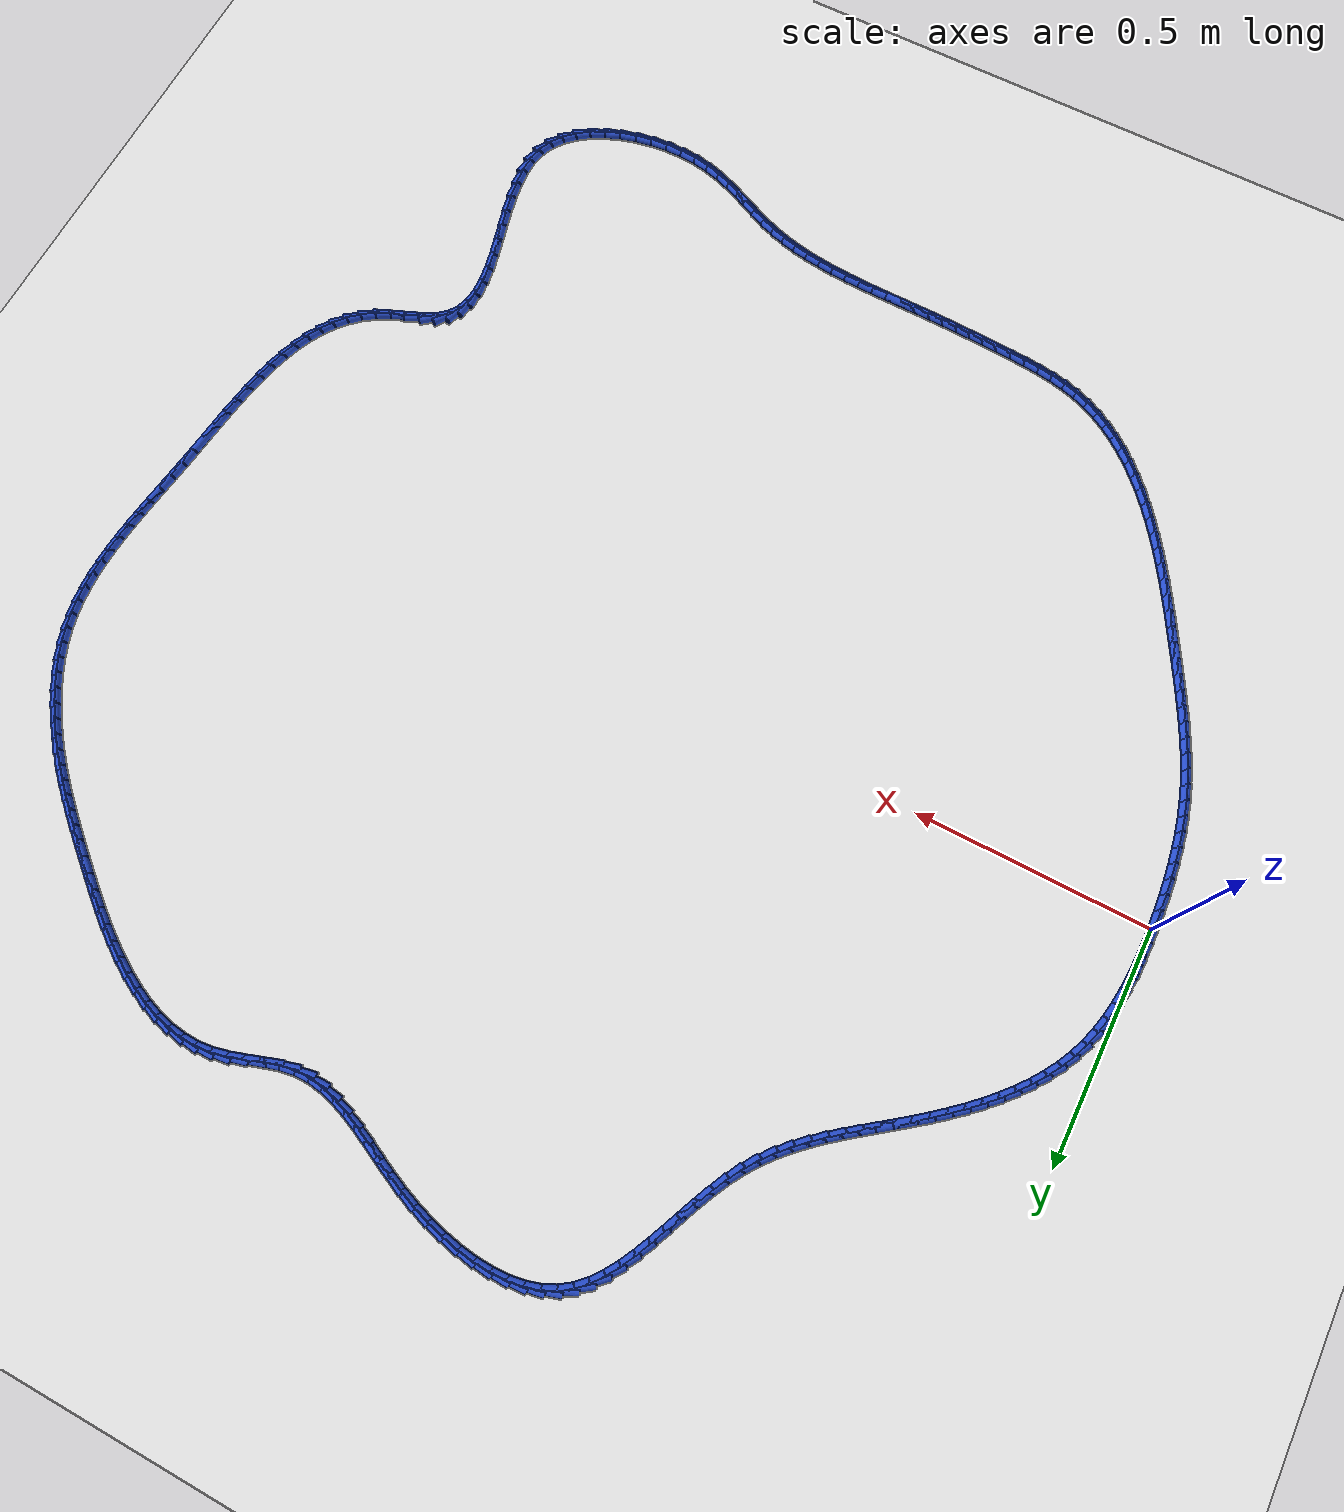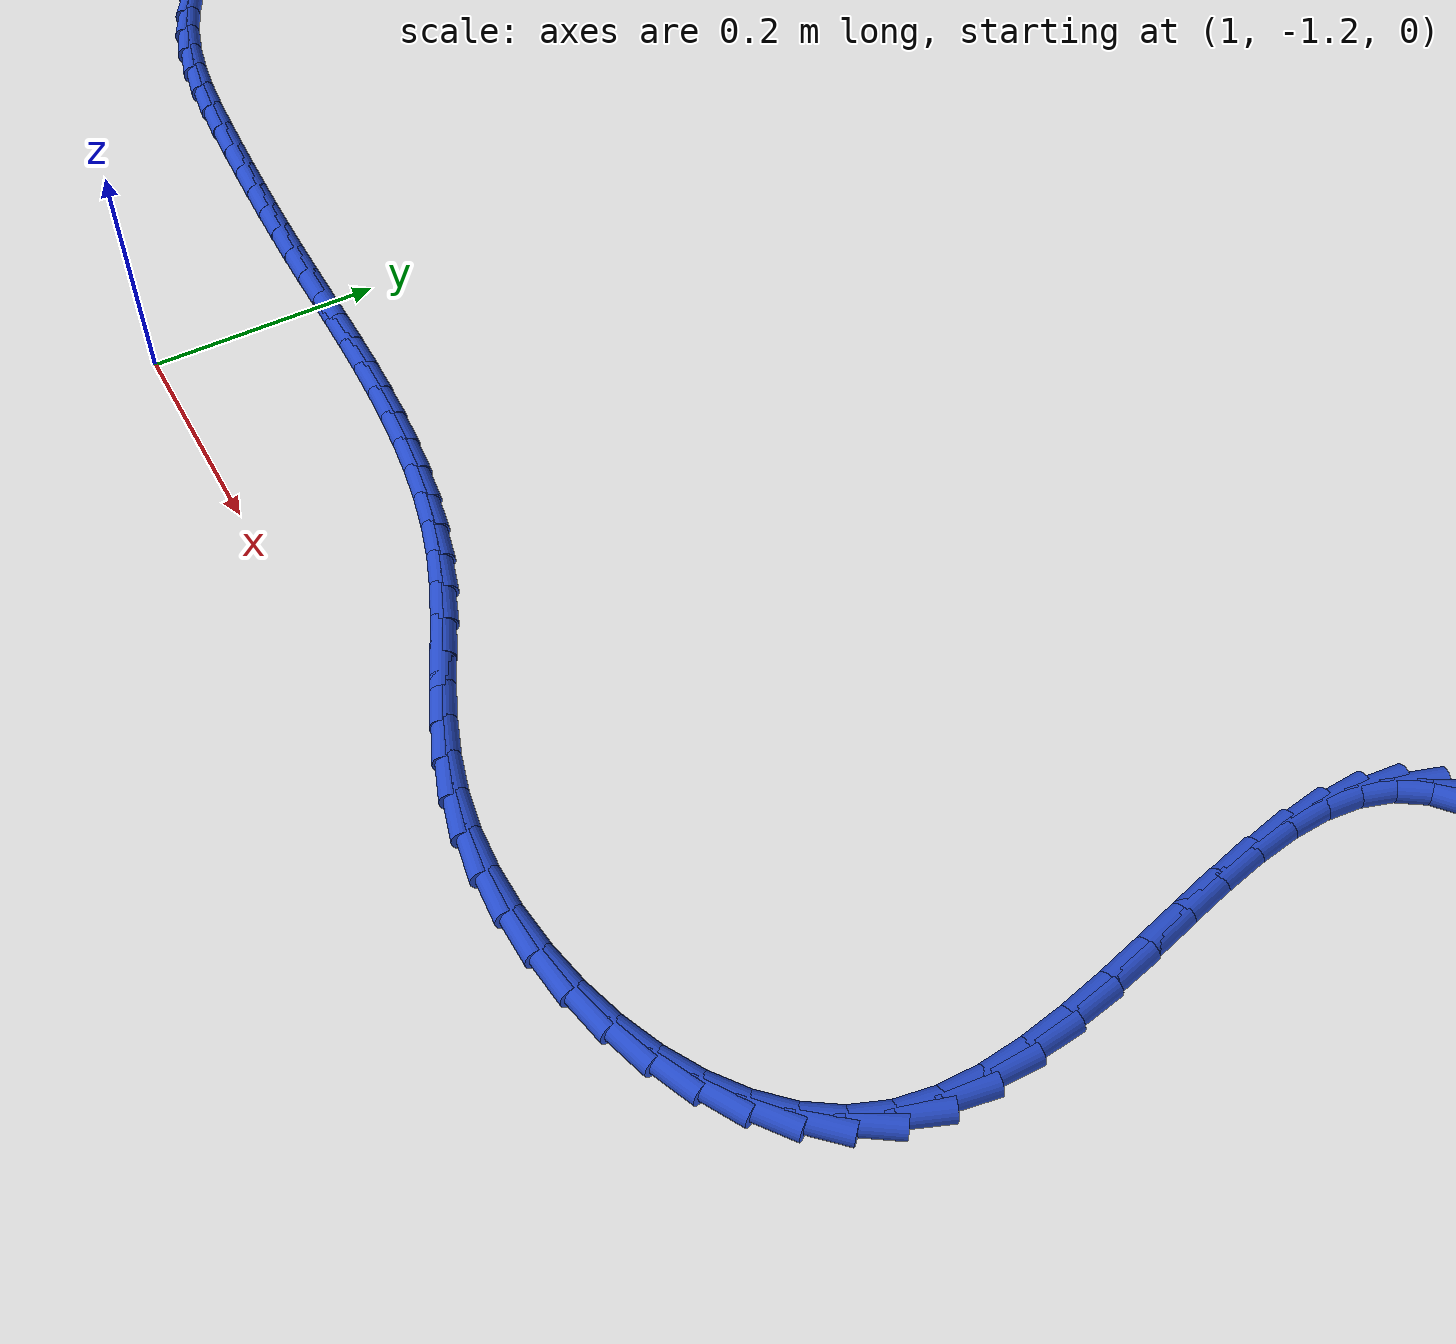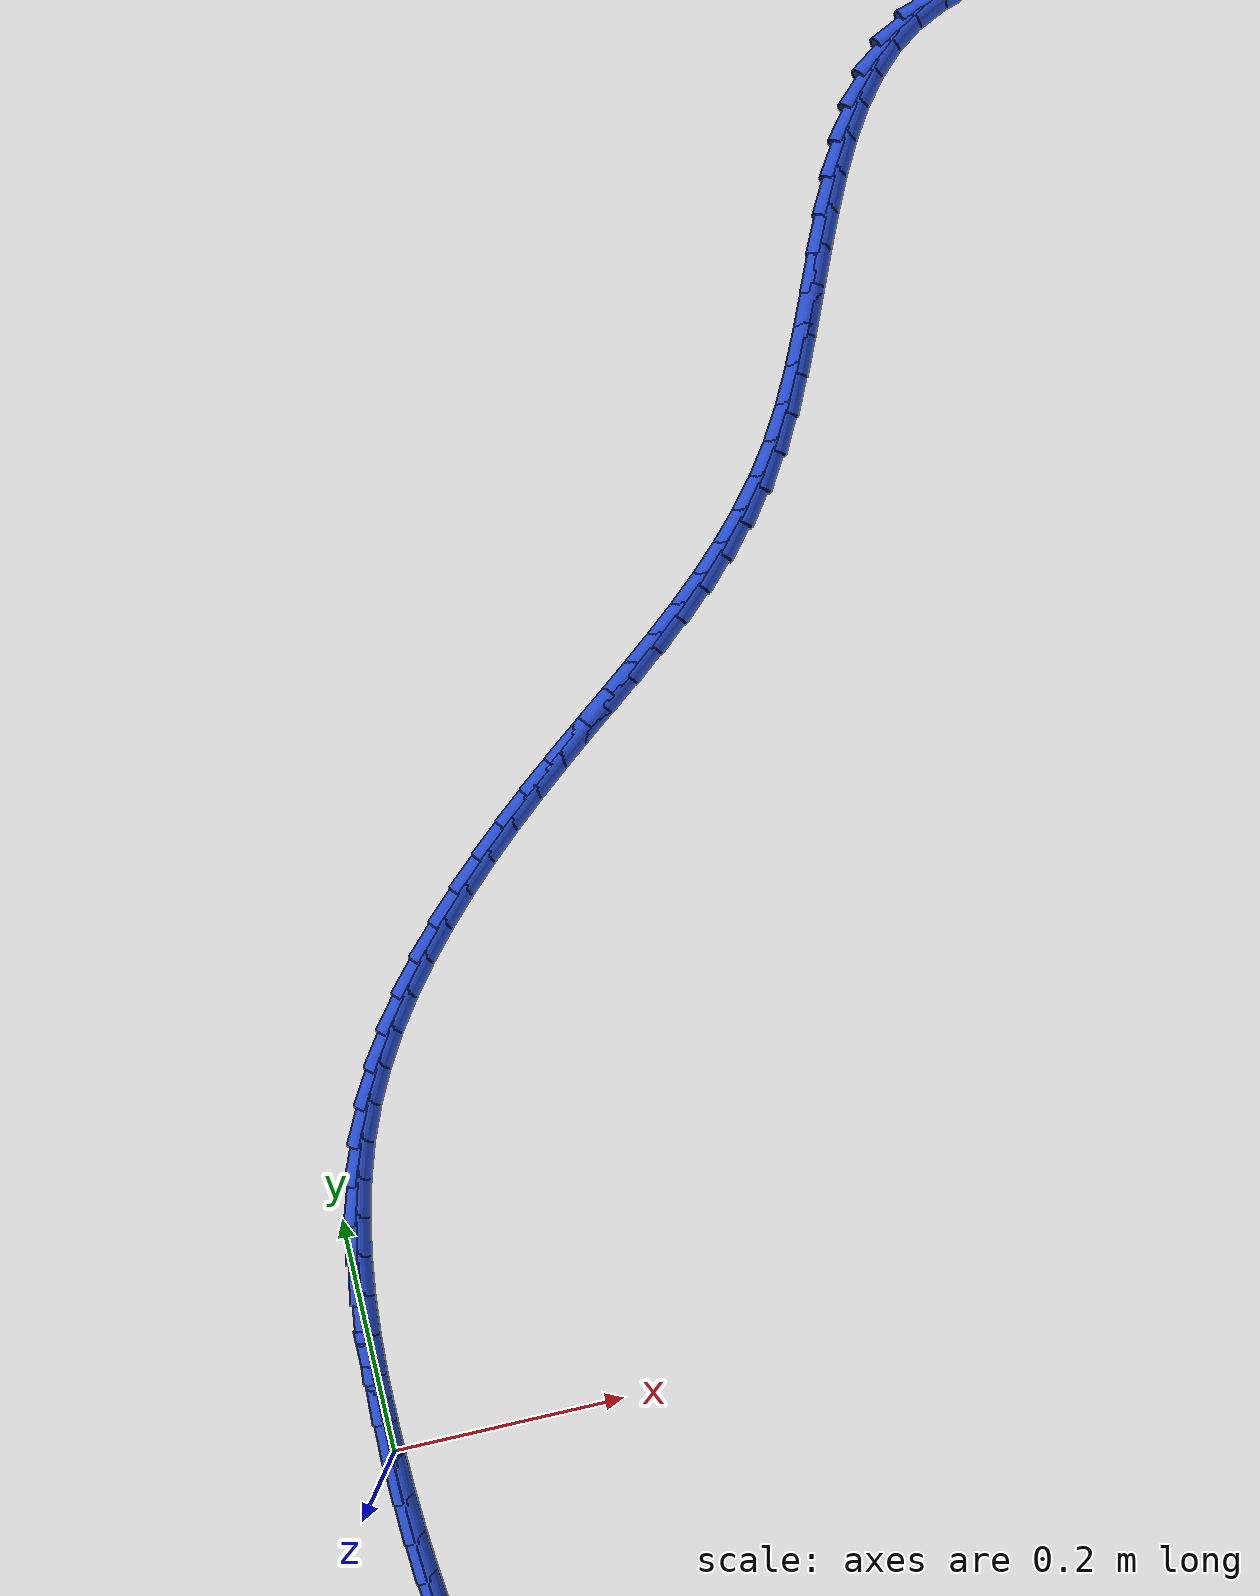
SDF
<sdf version="1.6">
 <world name="default">
  <light name="sun" type="directional">
   <pose>0 0 10 0 -0 0</pose>
   <diffuse>0.8 0.8 0.8 1</diffuse>
   <specular>0.2 0.2 0.2 1</specular>
   <attenuation>
    <range>1000</range>
    <constant>0.9</constant>
    <linear>0.01</linear>
    <quadratic>0.001</quadratic>
   </attenuation>
   <direction>-0.5 0.1 -0.9</direction>
  </light>
  <model name="ground_plane">
   <static>1</static>
   <link name="link">
    <collision name="collision">
     <geometry><plane><normal>0 0 1</normal><size>100 100</size></plane></geometry>
     <surface><friction><ode><mu>100</mu><mu2>50</mu2></ode></friction></surface>
    </collision>
    <visual name="visual">
     <cast_shadows>0</cast_shadows>
     <geometry><plane><normal>0 0 1</normal><size>100 100</size></plane></geometry>
     <material>
      <script><uri>file://media/materials/scripts/gazebo.material</uri><name>Gazebo/WhiteGlow</name></script>
     </material>
    </visual>
   </link>
  </model>
  <gravity>0 0 -9.8</gravity>
  <magnetic_field>6e-06 2.3e-05 -4.2e-05</magnetic_field>
  <atmosphere type="adiabatic"/>
  <physics name="default_physics" default="0" type="ode">
   <max_step_size>0.001</max_step_size>
   <real_time_factor>1</real_time_factor>
   <real_time_update_rate>1000</real_time_update_rate>
  </physics>
  <scene><ambient>0.4 0.4 0.4 1</ambient><background>0.7 0.7 0.7 1</background><shadows>1</shadows></scene>
  <spherical_coordinates>
   <surface_model>EARTH_WGS84</surface_model>
   <latitude_deg>0</latitude_deg>
   <longitude_deg>0</longitude_deg>
   <elevation>0</elevation>
   <heading_deg>0</heading_deg>
  </spherical_coordinates>
  <model name="line">
   <link name="link_0">
    <pose>1.0408340855860843e-17 2.7755575615628914e-17 0.01 0 1.57 -1.557937915153163</pose>
    <collision name="collision">
     <geometry><cylinder><radius>0.01</radius><length>0.08</length></cylinder></geometry>
    </collision>
    <visual name="visual">
     <material>
      <script><name>Gazebo/Blue</name><uri>file://media/materials/scripts/gazebo.material</uri></script>
     </material>
     <geometry><cylinder><radius>0.01</radius><length>0.08</length></cylinder></geometry>
    </visual>
   </link>
   <link name="link_1">
    <pose>-0.0004366516335810031 0.03395657102417911 0.01 0 1.57 1.557288796669142</pose>
    <collision name="collision">
     <geometry><cylinder><radius>0.01</radius><length>0.08</length></cylinder></geometry>
    </collision>
    <visual name="visual">
     <material>
      <script><name>Gazebo/Blue</name><uri>file://media/materials/scripts/gazebo.material</uri></script>
     </material>
     <geometry><cylinder><radius>0.01</radius><length>0.08</length></cylinder></geometry>
    </visual>
   </link>
   <link name="link_2">
    <pose>2.20297661370606e-05 0.06791196472825632 0.01 0 1.57 1.524633570331081</pose>
    <collision name="collision">
     <geometry><cylinder><radius>0.01</radius><length>0.08</length></cylinder></geometry>
    </collision>
    <visual name="visual">
     <material>
      <script><name>Gazebo/Blue</name><uri>file://media/materials/scripts/gazebo.material</uri></script>
     </material>
     <geometry><cylinder><radius>0.01</radius><length>0.08</length></cylinder></geometry>
    </visual>
   </link>
   <link name="link_3">
    <pose>0.001583885330539901 0.10172160020500445 0.01 0 1.57 1.4852973023227518</pose>
    <collision name="collision">
     <geometry><cylinder><radius>0.01</radius><length>0.08</length></cylinder></geometry>
    </collision>
    <visual name="visual">
     <material>
      <script><name>Gazebo/Blue</name><uri>file://media/materials/scripts/gazebo.material</uri></script>
     </material>
     <geometry><cylinder><radius>0.01</radius><length>0.08</length></cylinder></geometry>
    </visual>
   </link>
   <link name="link_4">
    <pose>0.004456756191013208 0.13524089654719626 0.01 0 1.57 1.438824625745498</pose>
    <collision name="collision">
     <geometry><cylinder><radius>0.01</radius><length>0.08</length></cylinder></geometry>
    </collision>
    <visual name="visual">
     <material>
      <script><name>Gazebo/Blue</name><uri>file://media/materials/scripts/gazebo.material</uri></script>
     </material>
     <geometry><cylinder><radius>0.01</radius><length>0.08</length></cylinder></geometry>
    </visual>
   </link>
   <link name="link_5">
    <pose>0.008848483478942688 0.16832527284760457 0.01 0 1.57 1.3847423070873557</pose>
    <collision name="collision">
     <geometry><cylinder><radius>0.01</radius><length>0.08</length></cylinder></geometry>
    </collision>
    <visual name="visual">
     <material>
      <script><name>Gazebo/Blue</name><uri>file://media/materials/scripts/gazebo.material</uri></script>
     </material>
     <geometry><cylinder><radius>0.01</radius><length>0.08</length></cylinder></geometry>
    </visual>
   </link>
   <link name="link_6">
    <pose>0.014966908325714024 0.200830148199002 0.01 0 1.57 1.322628793208983</pose>
    <collision name="collision">
     <geometry><cylinder><radius>0.01</radius><length>0.08</length></cylinder></geometry>
    </collision>
    <visual name="visual">
     <material>
      <script><name>Gazebo/Blue</name><uri>file://media/materials/scripts/gazebo.material</uri></script>
     </material>
     <geometry><cylinder><radius>0.01</radius><length>0.08</length></cylinder></geometry>
    </visual>
   </link>
   <link name="link_7">
    <pose>0.023019871862712912 0.23261094169416136 0.01 0 1.57 1.2522138872958029</pose>
    <collision name="collision">
     <geometry><cylinder><radius>0.01</radius><length>0.08</length></cylinder></geometry>
    </collision>
    <visual name="visual">
     <material>
      <script><name>Gazebo/Blue</name><uri>file://media/materials/scripts/gazebo.material</uri></script>
     </material>
     <geometry><cylinder><radius>0.01</radius><length>0.08</length></cylinder></geometry>
    </visual>
   </link>
   <link name="link_8">
    <pose>0.03321521522132507 0.2635230724258556 0.01 0 1.57 1.1736570817971768</pose>
    <collision name="collision">
     <geometry><cylinder><radius>0.01</radius><length>0.08</length></cylinder></geometry>
    </collision>
    <visual name="visual">
     <material>
      <script><name>Gazebo/Blue</name><uri>file://media/materials/scripts/gazebo.material</uri></script>
     </material>
     <geometry><cylinder><radius>0.01</radius><length>0.08</length></cylinder></geometry>
    </visual>
   </link>
   <link name="link_9">
    <pose>0.04575639282164466 0.2934239436651608 0.01 0 1.57 1.093315271874987</pose>
    <collision name="collision">
     <geometry><cylinder><radius>0.01</radius><length>0.08</length></cylinder></geometry>
    </collision>
    <visual name="visual">
     <material>
      <script><name>Gazebo/Blue</name><uri>file://media/materials/scripts/gazebo.material</uri></script>
     </material>
     <geometry><cylinder><radius>0.01</radius><length>0.08</length></cylinder></geometry>
    </visual>
   </link>
   <link name="link_10">
    <pose>0.06067151824599799 0.32225026809352914 0.01 0 1.57 1.0195763641413083</pose>
    <collision name="collision">
     <geometry><cylinder><radius>0.01</radius><length>0.08</length></cylinder></geometry>
    </collision>
    <visual name="visual">
     <material>
      <script><name>Gazebo/Blue</name><uri>file://media/materials/scripts/gazebo.material</uri></script>
     </material>
     <geometry><cylinder><radius>0.01</radius><length>0.08</length></cylinder></geometry>
    </visual>
   </link>
   <link name="link_11">
    <pose>0.07775811025583163 0.3500430600457663 0.01 0 1.57 0.9532256891473085</pose>
    <collision name="collision">
     <geometry><cylinder><radius>0.01</radius><length>0.08</length></cylinder></geometry>
    </collision>
    <visual name="visual">
     <material>
      <script><name>Gazebo/Blue</name><uri>file://media/materials/scripts/gazebo.material</uri></script>
     </material>
     <geometry><cylinder><radius>0.01</radius><length>0.08</length></cylinder></geometry>
    </visual>
   </link>
   <link name="link_12">
    <pose>0.096797989507644 0.3768504343557028 0.01 0 1.57 0.8941977770259731</pose>
    <collision name="collision">
     <geometry><cylinder><radius>0.01</radius><length>0.08</length></cylinder></geometry>
    </collision>
    <visual name="visual">
     <material>
      <script><name>Gazebo/Blue</name><uri>file://media/materials/scripts/gazebo.material</uri></script>
     </material>
     <geometry><cylinder><radius>0.01</radius><length>0.08</length></cylinder></geometry>
    </visual>
   </link>
   <link name="link_13">
    <pose>0.11757297665793337 0.4027205058571686 0.01 0 1.57 0.8422188590748143</pose>
    <collision name="collision">
     <geometry><cylinder><radius>0.01</radius><length>0.08</length></cylinder></geometry>
    </collision>
    <visual name="visual">
     <material>
      <script><name>Gazebo/Blue</name><uri>file://media/materials/scripts/gazebo.material</uri></script>
     </material>
     <geometry><cylinder><radius>0.01</radius><length>0.08</length></cylinder></geometry>
    </visual>
   </link>
   <link name="link_14">
    <pose>0.1398648923631981 0.42770138938399394 0.01 0 1.57 0.7969027888582101</pose>
    <collision name="collision">
     <geometry><cylinder><radius>0.01</radius><length>0.08</length></cylinder></geometry>
    </collision>
    <visual name="visual">
     <material>
      <script><name>Gazebo/Blue</name><uri>file://media/materials/scripts/gazebo.material</uri></script>
     </material>
     <geometry><cylinder><radius>0.01</radius><length>0.08</length></cylinder></geometry>
    </visual>
   </link>
   <link name="link_15">
    <pose>0.16345555727993652 0.45184119977000886 0.01 0 1.57 0.7578242402563893</pose>
    <collision name="collision">
     <geometry><cylinder><radius>0.01</radius><length>0.08</length></cylinder></geometry>
    </collision>
    <visual name="visual">
     <material>
      <script><name>Gazebo/Blue</name><uri>file://media/materials/scripts/gazebo.material</uri></script>
     </material>
     <geometry><cylinder><radius>0.01</radius><length>0.08</length></cylinder></geometry>
    </visual>
   </link>
   <link name="link_16">
    <pose>0.18812679206464697 0.4751880518490437 0.01 0 1.57 0.7245700439027598</pose>
    <collision name="collision">
     <geometry><cylinder><radius>0.01</radius><length>0.08</length></cylinder></geometry>
    </collision>
    <visual name="visual">
     <material>
      <script><name>Gazebo/Blue</name><uri>file://media/materials/scripts/gazebo.material</uri></script>
     </material>
     <geometry><cylinder><radius>0.01</radius><length>0.08</length></cylinder></geometry>
    </visual>
   </link>
   <link name="link_17">
    <pose>0.2136604173738278 0.49779006045492846 0.01 0 1.57 0.696773197397411</pose>
    <collision name="collision">
     <geometry><cylinder><radius>0.01</radius><length>0.08</length></cylinder></geometry>
    </collision>
    <visual name="visual">
     <material>
      <script><name>Gazebo/Blue</name><uri>file://media/materials/scripts/gazebo.material</uri></script>
     </material>
     <geometry><cylinder><radius>0.01</radius><length>0.08</length></cylinder></geometry>
    </visual>
   </link>
   <link name="link_18">
    <pose>0.23983825386397728 0.5196953404214933 0.01 0 1.57 0.6741349119335827</pose>
    <collision name="collision">
     <geometry><cylinder><radius>0.01</radius><length>0.08</length></cylinder></geometry>
    </collision>
    <visual name="visual">
     <material>
      <script><name>Gazebo/Blue</name><uri>file://media/materials/scripts/gazebo.material</uri></script>
     </material>
     <geometry><cylinder><radius>0.01</radius><length>0.08</length></cylinder></geometry>
    </visual>
   </link>
   <link name="link_19">
    <pose>0.26644212219164876 0.5409520065835117 0.01 0 1.57 0.6572586589582546</pose>
    <collision name="collision">
     <geometry><cylinder><radius>0.01</radius><length>0.08</length></cylinder></geometry>
    </collision>
    <visual name="visual">
     <material>
      <script><name>Gazebo/Blue</name><uri>file://media/materials/scripts/gazebo.material</uri></script>
     </material>
     <geometry><cylinder><radius>0.01</radius><length>0.08</length></cylinder></geometry>
    </visual>
   </link>
   <link name="link_20">
    <pose>0.29325597943236603 0.5616448412804551 0.01 0 1.57 0.6493689240649307</pose>
    <collision name="collision">
     <geometry><cylinder><radius>0.01</radius><length>0.08</length></cylinder></geometry>
    </collision>
    <visual name="visual">
     <material>
      <script><name>Gazebo/Blue</name><uri>file://media/materials/scripts/gazebo.material</uri></script>
     </material>
     <geometry><cylinder><radius>0.01</radius><length>0.08</length></cylinder></geometry>
    </visual>
   </link>
   <link name="link_21">
    <pose>0.320072252769558 0.5820039998922449 0.01 0 1.57 0.6514314391784285</pose>
    <collision name="collision">
     <geometry><cylinder><radius>0.01</radius><length>0.08</length></cylinder></geometry>
    </collision>
    <visual name="visual">
     <material>
      <script><name>Gazebo/Blue</name><uri>file://media/materials/scripts/gazebo.material</uri></script>
     </material>
     <geometry><cylinder><radius>0.01</radius><length>0.08</length></cylinder></geometry>
    </visual>
   </link>
   <link name="link_22">
    <pose>0.3466854681883977 0.6022956596764641 0.01 0 1.57 0.6636277277835771</pose>
    <collision name="collision">
     <geometry><cylinder><radius>0.01</radius><length>0.08</length></cylinder></geometry>
    </collision>
    <visual name="visual">
     <material>
      <script><name>Gazebo/Blue</name><uri>file://media/materials/scripts/gazebo.material</uri></script>
     </material>
     <geometry><cylinder><radius>0.01</radius><length>0.08</length></cylinder></geometry>
    </visual>
   </link>
   <link name="link_23">
    <pose>0.37289015167405754 0.622785997890695 0.01 0 1.57 0.6861358870570317</pose>
    <collision name="collision">
     <geometry><cylinder><radius>0.01</radius><length>0.08</length></cylinder></geometry>
    </collision>
    <visual name="visual">
     <material>
      <script><name>Gazebo/Blue</name><uri>file://media/materials/scripts/gazebo.material</uri></script>
     </material>
     <geometry><cylinder><radius>0.01</radius><length>0.08</length></cylinder></geometry>
    </visual>
   </link>
   <link name="link_24">
    <pose>0.39848082921170996 0.6437411917925197 0.01 0 1.57 0.719091253221694</pose>
    <collision name="collision">
     <geometry><cylinder><radius>0.01</radius><length>0.08</length></cylinder></geometry>
    </collision>
    <visual name="visual">
     <material>
      <script><name>Gazebo/Blue</name><uri>file://media/materials/scripts/gazebo.material</uri></script>
     </material>
     <geometry><cylinder><radius>0.01</radius><length>0.08</length></cylinder></geometry>
    </visual>
   </link>
   <link name="link_25">
    <pose>0.4232520267865276 0.6654274186395208 0.01 0 1.57 0.7625114891809333</pose>
    <collision name="collision">
     <geometry><cylinder><radius>0.01</radius><length>0.08</length></cylinder></geometry>
    </collision>
    <visual name="visual">
     <material>
      <script><name>Gazebo/Blue</name><uri>file://media/materials/scripts/gazebo.material</uri></script>
     </material>
     <geometry><cylinder><radius>0.01</radius><length>0.08</length></cylinder></geometry>
    </visual>
   </link>
   <link name="link_26">
    <pose>0.4469982703836833 0.688110855689281 0.01 0 1.57 0.8161875606576083</pose>
    <collision name="collision">
     <geometry><cylinder><radius>0.01</radius><length>0.08</length></cylinder></geometry>
    </collision>
    <visual name="visual">
     <material>
      <script><name>Gazebo/Blue</name><uri>file://media/materials/scripts/gazebo.material</uri></script>
     </material>
     <geometry><cylinder><radius>0.01</radius><length>0.08</length></cylinder></geometry>
    </visual>
   </link>
   <link name="link_27">
    <pose>0.46951408598834926 0.7120576801993824 0.01 0 1.57 0.879552467888</pose>
    <collision name="collision">
     <geometry><cylinder><radius>0.01</radius><length>0.08</length></cylinder></geometry>
    </collision>
    <visual name="visual">
     <material>
      <script><name>Gazebo/Blue</name><uri>file://media/materials/scripts/gazebo.material</uri></script>
     </material>
     <geometry><cylinder><radius>0.01</radius><length>0.08</length></cylinder></geometry>
    </visual>
   </link>
   <link name="link_28">
    <pose>0.49059399958569805 0.7375340694274075 0.01 0 1.57 0.951556543378179</pose>
    <collision name="collision">
     <geometry><cylinder><radius>0.01</radius><length>0.08</length></cylinder></geometry>
    </collision>
    <visual name="visual">
     <material>
      <script><name>Gazebo/Blue</name><uri>file://media/materials/scripts/gazebo.material</uri></script>
     </material>
     <geometry><cylinder><radius>0.01</radius><length>0.08</length></cylinder></geometry>
    </visual>
   </link>
   <link name="link_29">
    <pose>0.5100325371609027 0.7648062006309391 0.01 0 1.57 1.027840118348146</pose>
    <collision name="collision">
     <geometry><cylinder><radius>0.01</radius><length>0.08</length></cylinder></geometry>
    </collision>
    <visual name="visual">
     <material>
      <script><name>Gazebo/Blue</name><uri>file://media/materials/scripts/gazebo.material</uri></script>
     </material>
     <geometry><cylinder><radius>0.01</radius><length>0.08</length></cylinder></geometry>
    </visual>
   </link>
   <link name="link_30">
    <pose>0.5276859185326649 0.7940600403217871 0.01 0 1.57 1.0896895256035029</pose>
    <collision name="collision">
     <geometry><cylinder><radius>0.01</radius><length>0.08</length></cylinder></geometry>
    </collision>
    <visual name="visual">
     <material>
      <script><name>Gazebo/Blue</name><uri>file://media/materials/scripts/gazebo.material</uri></script>
     </material>
     <geometry><cylinder><radius>0.01</radius><length>0.08</length></cylinder></geometry>
    </visual>
   </link>
   <link name="link_31">
    <pose>0.5438143462708526 0.8249563200588297 0.01 0 1.57 1.131644790193717</pose>
    <collision name="collision">
     <geometry><cylinder><radius>0.01</radius><length>0.08</length></cylinder></geometry>
    </collision>
    <visual name="visual">
     <material>
      <script><name>Gazebo/Blue</name><uri>file://media/materials/scripts/gazebo.material</uri></script>
     </material>
     <geometry><cylinder><radius>0.01</radius><length>0.08</length></cylinder></geometry>
    </visual>
   </link>
   <link name="link_32">
    <pose>0.5588405799720534 0.8569444241787386 0.01 0 1.57 1.1553986535935807</pose>
    <collision name="collision">
     <geometry><cylinder><radius>0.01</radius><length>0.08</length></cylinder></geometry>
    </collision>
    <visual name="visual">
     <material>
      <script><name>Gazebo/Blue</name><uri>file://media/materials/scripts/gazebo.material</uri></script>
     </material>
     <geometry><cylinder><radius>0.01</radius><length>0.08</length></cylinder></geometry>
    </visual>
   </link>
   <link name="link_33">
    <pose>0.5731878234722747 0.8894731594438452 0.01 0 1.57 1.1618820573560587</pose>
    <collision name="collision">
     <geometry><cylinder><radius>0.01</radius><length>0.08</length></cylinder></geometry>
    </collision>
    <visual name="visual">
     <material>
      <script><name>Gazebo/Blue</name><uri>file://media/materials/scripts/gazebo.material</uri></script>
     </material>
     <geometry><cylinder><radius>0.01</radius><length>0.08</length></cylinder></geometry>
    </visual>
   </link>
   <link name="link_34">
    <pose>0.5872792806075242 0.9219913326164818 0.01 0 1.57 1.151109035983466</pose>
    <collision name="collision">
     <geometry><cylinder><radius>0.01</radius><length>0.08</length></cylinder></geometry>
    </collision>
    <visual name="visual">
     <material>
      <script><name>Gazebo/Blue</name><uri>file://media/materials/scripts/gazebo.material</uri></script>
     </material>
     <geometry><cylinder><radius>0.01</radius><length>0.08</length></cylinder></geometry>
    </visual>
   </link>
   <link name="link_35">
    <pose>0.6015381552138094 0.9539477504589801 0.01 0 1.57 1.1221009711172223</pose>
    <collision name="collision">
     <geometry><cylinder><radius>0.01</radius><length>0.08</length></cylinder></geometry>
    </collision>
    <visual name="visual">
     <material>
      <script><name>Gazebo/Blue</name><uri>file://media/materials/scripts/gazebo.material</uri></script>
     </material>
     <geometry><cylinder><radius>0.01</radius><length>0.08</length></cylinder></geometry>
    </visual>
   </link>
   <link name="link_36">
    <pose>0.6163876511271378 0.9847912197336722 0.01 0 1.57 1.0728419619575362</pose>
    <collision name="collision">
     <geometry><cylinder><radius>0.01</radius><length>0.08</length></cylinder></geometry>
    </collision>
    <visual name="visual">
     <material>
      <script><name>Gazebo/Blue</name><uri>file://media/materials/scripts/gazebo.material</uri></script>
     </material>
     <geometry><cylinder><radius>0.01</radius><length>0.08</length></cylinder></geometry>
    </visual>
   </link>
   <link name="link_37">
    <pose>0.6322509721835169 1.0139705472028895 0.01 0 1.57 1.0003422529258295</pose>
    <collision name="collision">
     <geometry><cylinder><radius>0.01</radius><length>0.08</length></cylinder></geometry>
    </collision>
    <visual name="visual">
     <material>
      <script><name>Gazebo/Blue</name><uri>file://media/materials/scripts/gazebo.material</uri></script>
     </material>
     <geometry><cylinder><radius>0.01</radius><length>0.08</length></cylinder></geometry>
    </visual>
   </link>
   <link name="link_38">
    <pose>0.6495513222189545 1.0409345396289647 0.01 0 1.57 0.9010492410780814</pose>
    <collision name="collision">
     <geometry><cylinder><radius>0.01</radius><length>0.08</length></cylinder></geometry>
    </collision>
    <visual name="visual">
     <material>
      <script><name>Gazebo/Blue</name><uri>file://media/materials/scripts/gazebo.material</uri></script>
     </material>
     <geometry><cylinder><radius>0.01</radius><length>0.08</length></cylinder></geometry>
    </visual>
   </link>
   <link name="link_39">
    <pose>0.6687119050694581 1.0651320037742291 0.01 0 1.57 0.7720665639344656</pose>
    <collision name="collision">
     <geometry><cylinder><radius>0.01</radius><length>0.08</length></cylinder></geometry>
    </collision>
    <visual name="visual">
     <material>
      <script><name>Gazebo/Blue</name><uri>file://media/materials/scripts/gazebo.material</uri></script>
     </material>
     <geometry><cylinder><radius>0.01</radius><length>0.08</length></cylinder></geometry>
    </visual>
   </link>
   <link name="link_40">
    <pose>0.6901559245710348 1.0860117464010144 0.01 0 1.57 0.6137972136080931</pose>
    <collision name="collision">
     <geometry><cylinder><radius>0.01</radius><length>0.08</length></cylinder></geometry>
    </collision>
    <visual name="visual">
     <material>
      <script><name>Gazebo/Blue</name><uri>file://media/materials/scripts/gazebo.material</uri></script>
     </material>
     <geometry><cylinder><radius>0.01</radius><length>0.08</length></cylinder></geometry>
    </visual>
   </link>
   <link name="link_41">
    <pose>0.7143033924844925 1.1030257150771983 0.01 0 1.57 0.4451304729784368</pose>
    <collision name="collision">
     <geometry><cylinder><radius>0.01</radius><length>0.08</length></cylinder></geometry>
    </collision>
    <visual name="visual">
     <material>
      <script><name>Gazebo/Blue</name><uri>file://media/materials/scripts/gazebo.material</uri></script>
     </material>
     <geometry><cylinder><radius>0.01</radius><length>0.08</length></cylinder></geometry>
    </visual>
   </link>
   <link name="link_42">
    <pose>0.7412938163416424 1.1159018562687966 0.01 0 1.57 0.29489687600832765</pose>
    <collision name="collision">
     <geometry><cylinder><radius>0.01</radius><length>0.08</length></cylinder></geometry>
    </collision>
    <visual name="visual">
     <material>
      <script><name>Gazebo/Blue</name><uri>file://media/materials/scripts/gazebo.material</uri></script>
     </material>
     <geometry><cylinder><radius>0.01</radius><length>0.08</length></cylinder></geometry>
    </visual>
   </link>
   <link name="link_43">
    <pose>0.7707711569409348 1.1248557039298024 0.01 0 1.57 0.16629822384729626</pose>
    <collision name="collision">
     <geometry><cylinder><radius>0.01</radius><length>0.08</length></cylinder></geometry>
    </collision>
    <visual name="visual">
     <material>
      <script><name>Gazebo/Blue</name><uri>file://media/materials/scripts/gazebo.material</uri></script>
     </material>
     <geometry><cylinder><radius>0.01</radius><length>0.08</length></cylinder></geometry>
    </visual>
   </link>
   <link name="link_44">
    <pose>0.8023287581900675 1.1301525959195724 0.01 0 1.57 0.057271187827695885</pose>
    <collision name="collision">
     <geometry><cylinder><radius>0.01</radius><length>0.08</length></cylinder></geometry>
    </collision>
    <visual name="visual">
     <material>
      <script><name>Gazebo/Blue</name><uri>file://media/materials/scripts/gazebo.material</uri></script>
     </material>
     <geometry><cylinder><radius>0.01</radius><length>0.08</length></cylinder></geometry>
    </visual>
   </link>
   <link name="link_45">
    <pose>0.8355599639967382 1.1320578700974642 0.01 0 1.57 -0.03537859737396286</pose>
    <collision name="collision">
     <geometry><cylinder><radius>0.01</radius><length>0.08</length></cylinder></geometry>
    </collision>
    <visual name="visual">
     <material>
      <script><name>Gazebo/Blue</name><uri>file://media/materials/scripts/gazebo.material</uri></script>
     </material>
     <geometry><cylinder><radius>0.01</radius><length>0.08</length></cylinder></geometry>
    </visual>
   </link>
   <link name="link_46">
    <pose>0.8700581182686442 1.1308368643228346 0.01 0 1.57 -0.11493597282656826</pose>
    <collision name="collision">
     <geometry><cylinder><radius>0.01</radius><length>0.08</length></cylinder></geometry>
    </collision>
    <visual name="visual">
     <material>
      <script><name>Gazebo/Blue</name><uri>file://media/materials/scripts/gazebo.material</uri></script>
     </material>
     <geometry><cylinder><radius>0.01</radius><length>0.08</length></cylinder></geometry>
    </visual>
   </link>
   <link name="link_47">
    <pose>0.9054165649134827 1.12675491645504 0.01 0 1.57 -0.18434392155907342</pose>
    <collision name="collision">
     <geometry><cylinder><radius>0.01</radius><length>0.08</length></cylinder></geometry>
    </collision>
    <visual name="visual">
     <material>
      <script><name>Gazebo/Blue</name><uri>file://media/materials/scripts/gazebo.material</uri></script>
     </material>
     <geometry><cylinder><radius>0.01</radius><length>0.08</length></cylinder></geometry>
    </visual>
   </link>
   <link name="link_48">
    <pose>0.9412286478389515 1.1200773643534379 0.01 0 1.57 -0.24610832803351923</pose>
    <collision name="collision">
     <geometry><cylinder><radius>0.01</radius><length>0.08</length></cylinder></geometry>
    </collision>
    <visual name="visual">
     <material>
      <script><name>Gazebo/Blue</name><uri>file://media/materials/scripts/gazebo.material</uri></script>
     </material>
     <geometry><cylinder><radius>0.01</radius><length>0.08</length></cylinder></geometry>
    </visual>
   </link>
   <link name="link_49">
    <pose>0.9770877109527485 1.1110695458773852 0.01 0 1.57 -0.3023506868403747</pose>
    <collision name="collision">
     <geometry><cylinder><radius>0.01</radius><length>0.08</length></cylinder></geometry>
    </collision>
    <visual name="visual">
     <material>
      <script><name>Gazebo/Blue</name><uri>file://media/materials/scripts/gazebo.material</uri></script>
     </material>
     <geometry><cylinder><radius>0.01</radius><length>0.08</length></cylinder></geometry>
    </visual>
   </link>
   <link name="link_50">
    <pose>1.0125870981625706 1.0999967988862385 0.01 0 1.57 -0.35491025318495983</pose>
    <collision name="collision">
     <geometry><cylinder><radius>0.01</radius><length>0.08</length></cylinder></geometry>
    </collision>
    <visual name="visual">
     <material>
      <script><name>Gazebo/Blue</name><uri>file://media/materials/scripts/gazebo.material</uri></script>
     </material>
     <geometry><cylinder><radius>0.01</radius><length>0.08</length></cylinder></geometry>
    </visual>
   </link>
   <link name="link_51">
    <pose>1.0473202879229055 1.087124572644747 0.01 0 1.57 -0.40133344969270723</pose>
    <collision name="collision">
     <geometry><cylinder><radius>0.01</radius><length>0.08</length></cylinder></geometry>
    </collision>
    <visual name="visual">
     <material>
      <script><name>Gazebo/Blue</name><uri>file://media/materials/scripts/gazebo.material</uri></script>
     </material>
     <geometry><cylinder><radius>0.01</radius><length>0.08</length></cylinder></geometry>
    </visual>
   </link>
   <link name="link_52">
    <pose>1.0810119788744577 1.072826967365465 0.01 0 1.57 -0.4304201294191563</pose>
    <collision name="collision">
     <geometry><cylinder><radius>0.01</radius><length>0.08</length></cylinder></geometry>
    </collision>
    <visual name="visual">
     <material>
      <script><name>Gazebo/Blue</name><uri>file://media/materials/scripts/gazebo.material</uri></script>
     </material>
     <geometry><cylinder><radius>0.01</radius><length>0.08</length></cylinder></geometry>
    </visual>
   </link>
   <link name="link_53">
    <pose>1.1137633748970166 1.057789831416926 0.01 0 1.57 -0.43948715836565483</pose>
    <collision name="collision">
     <geometry><cylinder><radius>0.01</radius><length>0.08</length></cylinder></geometry>
    </collision>
    <visual name="visual">
     <material>
      <script><name>Gazebo/Blue</name><uri>file://media/materials/scripts/gazebo.material</uri></script>
     </material>
     <geometry><cylinder><radius>0.01</radius><length>0.08</length></cylinder></geometry>
    </visual>
   </link>
   <link name="link_54">
    <pose>1.1457427863492065 1.042754577656174 0.01 0 1.57 -0.42742649762145185</pose>
    <collision name="collision">
     <geometry><cylinder><radius>0.01</radius><length>0.08</length></cylinder></geometry>
    </collision>
    <visual name="visual">
     <material>
      <script><name>Gazebo/Blue</name><uri>file://media/materials/scripts/gazebo.material</uri></script>
     </material>
     <geometry><cylinder><radius>0.01</radius><length>0.08</length></cylinder></geometry>
    </visual>
   </link>
   <link name="link_55">
    <pose>1.1771185235896513 1.028462618940252 0.01 0 1.57 -0.39245983784581384</pose>
    <collision name="collision">
     <geometry><cylinder><radius>0.01</radius><length>0.08</length></cylinder></geometry>
    </collision>
    <visual name="visual">
     <material>
      <script><name>Gazebo/Blue</name><uri>file://media/materials/scripts/gazebo.material</uri></script>
     </material>
     <geometry><cylinder><radius>0.01</radius><length>0.08</length></cylinder></geometry>
    </visual>
   </link>
   <link name="link_56">
    <pose>1.2080588969769754 1.0156553681262033 0.01 0 1.57 -0.33217960032265254</pose>
    <collision name="collision">
     <geometry><cylinder><radius>0.01</radius><length>0.08</length></cylinder></geometry>
    </collision>
    <visual name="visual">
     <material>
      <script><name>Gazebo/Blue</name><uri>file://media/materials/scripts/gazebo.material</uri></script>
     </material>
     <geometry><cylinder><radius>0.01</radius><length>0.08</length></cylinder></geometry>
    </visual>
   </link>
   <link name="link_57">
    <pose>1.2387322168698027 1.005074238071071 0.01 0 1.57 -0.2440534902768936</pose>
    <collision name="collision">
     <geometry><cylinder><radius>0.01</radius><length>0.08</length></cylinder></geometry>
    </collision>
    <visual name="visual">
     <material>
      <script><name>Gazebo/Blue</name><uri>file://media/materials/scripts/gazebo.material</uri></script>
     </material>
     <geometry><cylinder><radius>0.01</radius><length>0.08</length></cylinder></geometry>
    </visual>
   </link>
   <link name="link_58">
    <pose>1.269306793626757 0.9974606416318995 0.01 0 1.57 -0.12673618728374014</pose>
    <collision name="collision">
     <geometry><cylinder><radius>0.01</radius><length>0.08</length></cylinder></geometry>
    </collision>
    <visual name="visual">
     <material>
      <script><name>Gazebo/Blue</name><uri>file://media/materials/scripts/gazebo.material</uri></script>
     </material>
     <geometry><cylinder><radius>0.01</radius><length>0.08</length></cylinder></geometry>
    </visual>
   </link>
   <link name="link_59">
    <pose>1.299950937606464 0.9935559916657318 0.01 0 1.57 0.01766893961338835</pose>
    <collision name="collision">
     <geometry><cylinder><radius>0.01</radius><length>0.08</length></cylinder></geometry>
    </collision>
    <visual name="visual">
     <material>
      <script><name>Gazebo/Blue</name><uri>file://media/materials/scripts/gazebo.material</uri></script>
     </material>
     <geometry><cylinder><radius>0.01</radius><length>0.08</length></cylinder></geometry>
    </visual>
   </link>
   <link name="link_60">
    <pose>1.3308329591675458 0.9941017010296109 0.01 0 1.57 0.17495033114294778</pose>
    <collision name="collision">
     <geometry><cylinder><radius>0.01</radius><length>0.08</length></cylinder></geometry>
    </collision>
    <visual name="visual">
     <material>
      <script><name>Gazebo/Blue</name><uri>file://media/materials/scripts/gazebo.material</uri></script>
     </material>
     <geometry><cylinder><radius>0.01</radius><length>0.08</length></cylinder></geometry>
    </visual>
   </link>
   <link name="link_61">
    <pose>1.3621005171388616 0.9996284731561782 0.01 0 1.57 0.2852929375083193</pose>
    <collision name="collision">
     <geometry><cylinder><radius>0.01</radius><length>0.08</length></cylinder></geometry>
    </collision>
    <visual name="visual">
     <material>
      <script><name>Gazebo/Blue</name><uri>file://media/materials/scripts/gazebo.material</uri></script>
     </material>
     <geometry><cylinder><radius>0.01</radius><length>0.08</length></cylinder></geometry>
    </visual>
   </link>
   <link name="link_62">
    <pose>1.3937285546589575 1.0089047776822078 0.01 0 1.57 0.32993432730314515</pose>
    <collision name="collision">
     <geometry><cylinder><radius>0.01</radius><length>0.08</length></cylinder></geometry>
    </collision>
    <visual name="visual">
     <material>
      <script><name>Gazebo/Blue</name><uri>file://media/materials/scripts/gazebo.material</uri></script>
     </material>
     <geometry><cylinder><radius>0.01</radius><length>0.08</length></cylinder></geometry>
    </visual>
   </link>
   <link name="link_63">
    <pose>1.4256059786622342 1.0198212490788097 0.01 0 1.57 0.3152472145296275</pose>
    <collision name="collision">
     <geometry><cylinder><radius>0.01</radius><length>0.08</length></cylinder></geometry>
    </collision>
    <visual name="visual">
     <material>
      <script><name>Gazebo/Blue</name><uri>file://media/materials/scripts/gazebo.material</uri></script>
     </material>
     <geometry><cylinder><radius>0.01</radius><length>0.08</length></cylinder></geometry>
    </visual>
   </link>
   <link name="link_64">
    <pose>1.4576210670239298 1.0302621034696458 0.01 0 1.57 0.2402660732697191</pose>
    <collision name="collision">
     <geometry><cylinder><radius>0.01</radius><length>0.08</length></cylinder></geometry>
    </collision>
    <visual name="visual">
     <material>
      <script><name>Gazebo/Blue</name><uri>file://media/materials/scripts/gazebo.material</uri></script>
     </material>
     <geometry><cylinder><radius>0.01</radius><length>0.08</length></cylinder></geometry>
    </visual>
   </link>
   <link name="link_65">
    <pose>1.4896621130251764 1.0381121189993925 0.01 0 1.57 0.1153322933310828</pose>
    <collision name="collision">
     <geometry><cylinder><radius>0.01</radius><length>0.08</length></cylinder></geometry>
    </collision>
    <visual name="visual">
     <material>
      <script><name>Gazebo/Blue</name><uri>file://media/materials/scripts/gazebo.material</uri></script>
     </material>
     <geometry><cylinder><radius>0.01</radius><length>0.08</length></cylinder></geometry>
    </visual>
   </link>
   <link name="link_66">
    <pose>1.5216327529966942 1.0418158023687274 0.01 0 1.57 -0.012185239544491975</pose>
    <collision name="collision">
     <geometry><cylinder><radius>0.01</radius><length>0.08</length></cylinder></geometry>
    </collision>
    <visual name="visual">
     <material>
      <script><name>Gazebo/Blue</name><uri>file://media/materials/scripts/gazebo.material</uri></script>
     </material>
     <geometry><cylinder><radius>0.01</radius><length>0.08</length></cylinder></geometry>
    </visual>
   </link>
   <link name="link_67">
    <pose>1.5534807572259863 1.0414277075998775 0.01 0 1.57 -0.12986655619384777</pose>
    <collision name="collision">
     <geometry><cylinder><radius>0.01</radius><length>0.08</length></cylinder></geometry>
    </collision>
    <visual name="visual">
     <material>
      <script><name>Gazebo/Blue</name><uri>file://media/materials/scripts/gazebo.material</uri></script>
     </material>
     <geometry><cylinder><radius>0.01</radius><length>0.08</length></cylinder></geometry>
    </visual>
   </link>
   <link name="link_68">
    <pose>1.5851617830375213 1.0372901150751321 0.01 0 1.57 -0.23530702625468602</pose>
    <collision name="collision">
     <geometry><cylinder><radius>0.01</radius><length>0.08</length></cylinder></geometry>
    </collision>
    <visual name="visual">
     <material>
      <script><name>Gazebo/Blue</name><uri>file://media/materials/scripts/gazebo.material</uri></script>
     </material>
     <geometry><cylinder><radius>0.01</radius><length>0.08</length></cylinder></geometry>
    </visual>
   </link>
   <link name="link_69">
    <pose>1.6166314877557653 1.0297453051767809 0.01 0 1.57 -0.3276515764144629</pose>
    <collision name="collision">
     <geometry><cylinder><radius>0.01</radius><length>0.08</length></cylinder></geometry>
    </collision>
    <visual name="visual">
     <material>
      <script><name>Gazebo/Blue</name><uri>file://media/materials/scripts/gazebo.material</uri></script>
     </material>
     <geometry><cylinder><radius>0.01</radius><length>0.08</length></cylinder></geometry>
    </visual>
   </link>
   <link name="link_70">
    <pose>1.6478455287051874 1.0191355582871136 0.01 0 1.57 -0.40717232580845236</pose>
    <collision name="collision">
     <geometry><cylinder><radius>0.01</radius><length>0.08</length></cylinder></geometry>
    </collision>
    <visual name="visual">
     <material>
      <script><name>Gazebo/Blue</name><uri>file://media/materials/scripts/gazebo.material</uri></script>
     </material>
     <geometry><cylinder><radius>0.01</radius><length>0.08</length></cylinder></geometry>
    </visual>
   </link>
   <link name="link_71">
    <pose>1.6787595632102545 1.0058031547884199 0.01 0 1.57 -0.4747837799427998</pose>
    <collision name="collision">
     <geometry><cylinder><radius>0.01</radius><length>0.08</length></cylinder></geometry>
    </collision>
    <visual name="visual">
     <material>
      <script><name>Gazebo/Blue</name><uri>file://media/materials/scripts/gazebo.material</uri></script>
     </material>
     <geometry><cylinder><radius>0.01</radius><length>0.08</length></cylinder></geometry>
    </visual>
   </link>
   <link name="link_72">
    <pose>1.7093292485954343 0.9900903750629889 0.01 0 1.57 -0.5316588310208041</pose>
    <collision name="collision">
     <geometry><cylinder><radius>0.01</radius><length>0.08</length></cylinder></geometry>
    </collision>
    <visual name="visual">
     <material>
      <script><name>Gazebo/Blue</name><uri>file://media/materials/scripts/gazebo.material</uri></script>
     </material>
     <geometry><cylinder><radius>0.01</radius><length>0.08</length></cylinder></geometry>
    </visual>
   </link>
   <link name="link_73">
    <pose>1.7395102421851947 0.9723394994931107 0.01 0 1.57 -0.5789824809146885</pose>
    <collision name="collision">
     <geometry><cylinder><radius>0.01</radius><length>0.08</length></cylinder></geometry>
    </collision>
    <visual name="visual">
     <material>
      <script><name>Gazebo/Blue</name><uri>file://media/materials/scripts/gazebo.material</uri></script>
     </material>
     <geometry><cylinder><radius>0.01</radius><length>0.08</length></cylinder></geometry>
    </visual>
   </link>
   <link name="link_74">
    <pose>1.7692582013040037 0.9528928084610749 0.01 0 1.57 -0.6178171866591782</pose>
    <collision name="collision">
     <geometry><cylinder><radius>0.01</radius><length>0.08</length></cylinder></geometry>
    </collision>
    <visual name="visual">
     <material>
      <script><name>Gazebo/Blue</name><uri>file://media/materials/scripts/gazebo.material</uri></script>
     </material>
     <geometry><cylinder><radius>0.01</radius><length>0.08</length></cylinder></geometry>
    </visual>
   </link>
   <link name="link_75">
    <pose>1.7985287832763275 0.9320925823491713 0.01 0 1.57 -0.6490396953476041</pose>
    <collision name="collision">
     <geometry><cylinder><radius>0.01</radius><length>0.08</length></cylinder></geometry>
    </collision>
    <visual name="visual">
     <material>
      <script><name>Gazebo/Blue</name><uri>file://media/materials/scripts/gazebo.material</uri></script>
     </material>
     <geometry><cylinder><radius>0.01</radius><length>0.08</length></cylinder></geometry>
    </visual>
   </link>
   <link name="link_76">
    <pose>1.8272776454266353 0.9102811015396886 0.01 0 1.57 -0.673316021401777</pose>
    <collision name="collision">
     <geometry><cylinder><radius>0.01</radius><length>0.08</length></cylinder></geometry>
    </collision>
    <visual name="visual">
     <material>
      <script><name>Gazebo/Blue</name><uri>file://media/materials/scripts/gazebo.material</uri></script>
     </material>
     <geometry><cylinder><radius>0.01</radius><length>0.08</length></cylinder></geometry>
    </visual>
   </link>
   <link name="link_77">
    <pose>1.8554604450793946 0.8878006464149175 0.01 0 1.57 -0.6910918271109545</pose>
    <collision name="collision">
     <geometry><cylinder><radius>0.01</radius><length>0.08</length></cylinder></geometry>
    </collision>
    <visual name="visual">
     <material>
      <script><name>Gazebo/Blue</name><uri>file://media/materials/scripts/gazebo.material</uri></script>
     </material>
     <geometry><cylinder><radius>0.01</radius><length>0.08</length></cylinder></geometry>
    </visual>
   </link>
   <link name="link_78">
    <pose>1.8830328395590723 0.8649934973571467 0.01 0 1.57 -0.7025835865334096</pose>
    <collision name="collision">
     <geometry><cylinder><radius>0.01</radius><length>0.08</length></cylinder></geometry>
    </collision>
    <visual name="visual">
     <material>
      <script><name>Gazebo/Blue</name><uri>file://media/materials/scripts/gazebo.material</uri></script>
     </material>
     <geometry><cylinder><radius>0.01</radius><length>0.08</length></cylinder></geometry>
    </visual>
   </link>
   <link name="link_79">
    <pose>1.909950486190136 0.8422019347486666 0.01 0 1.57 -0.7085103948531339</pose>
    <collision name="collision">
     <geometry><cylinder><radius>0.01</radius><length>0.08</length></cylinder></geometry>
    </collision>
    <visual name="visual">
     <material>
      <script><name>Gazebo/Blue</name><uri>file://media/materials/scripts/gazebo.material</uri></script>
     </material>
     <geometry><cylinder><radius>0.01</radius><length>0.08</length></cylinder></geometry>
    </visual>
   </link>
   <link name="link_80">
    <pose>1.9361720523402126 0.8197315769355193 0.01 0 1.57 -0.7158279394785463</pose>
    <collision name="collision">
     <geometry><cylinder><radius>0.01</radius><length>0.08</length></cylinder></geometry>
    </collision>
    <visual name="visual">
     <material>
      <script><name>Gazebo/Blue</name><uri>file://media/materials/scripts/gazebo.material</uri></script>
     </material>
     <geometry><cylinder><radius>0.01</radius><length>0.08</length></cylinder></geometry>
    </visual>
   </link>
   <link name="link_81">
    <pose>1.9616845314832105 0.7975430330127901 0.01 0 1.57 -0.7285683098272168</pose>
    <collision name="collision">
     <geometry><cylinder><radius>0.01</radius><length>0.08</length></cylinder></geometry>
    </collision>
    <visual name="visual">
     <material>
      <script><name>Gazebo/Blue</name><uri>file://media/materials/scripts/gazebo.material</uri></script>
     </material>
     <geometry><cylinder><radius>0.01</radius><length>0.08</length></cylinder></geometry>
    </visual>
   </link>
   <link name="link_82">
    <pose>1.9864904558289005 0.7754076517668419 0.01 0 1.57 -0.7468682749466197</pose>
    <collision name="collision">
     <geometry><cylinder><radius>0.01</radius><length>0.08</length></cylinder></geometry>
    </collision>
    <visual name="visual">
     <material>
      <script><name>Gazebo/Blue</name><uri>file://media/materials/scripts/gazebo.material</uri></script>
     </material>
     <geometry><cylinder><radius>0.01</radius><length>0.08</length></cylinder></geometry>
    </visual>
   </link>
   <link name="link_83">
    <pose>2.0105925173759043 0.7530948357711922 0.01 0 1.57 -0.7706547188329912</pose>
    <collision name="collision">
     <geometry><cylinder><radius>0.01</radius><length>0.08</length></cylinder></geometry>
    </collision>
    <visual name="visual">
     <material>
      <script><name>Gazebo/Blue</name><uri>file://media/materials/scripts/gazebo.material</uri></script>
     </material>
     <geometry><cylinder><radius>0.01</radius><length>0.08</length></cylinder></geometry>
    </visual>
   </link>
   <link name="link_84">
    <pose>2.0339934081228437 0.7303739875993593 0.01 0 1.57 -0.7996620433764371</pose>
    <collision name="collision">
     <geometry><cylinder><radius>0.01</radius><length>0.08</length></cylinder></geometry>
    </collision>
    <visual name="visual">
     <material>
      <script><name>Gazebo/Blue</name><uri>file://media/materials/scripts/gazebo.material</uri></script>
     </material>
     <geometry><cylinder><radius>0.01</radius><length>0.08</length></cylinder></geometry>
    </visual>
   </link>
   <link name="link_85">
    <pose>2.0566958200683403 0.7070145098248608 0.01 0 1.57 -0.8334214215739584</pose>
    <collision name="collision">
     <geometry><cylinder><radius>0.01</radius><length>0.08</length></cylinder></geometry>
    </collision>
    <visual name="visual">
     <material>
      <script><name>Gazebo/Blue</name><uri>file://media/materials/scripts/gazebo.material</uri></script>
     </material>
     <geometry><cylinder><radius>0.01</radius><length>0.08</length></cylinder></geometry>
    </visual>
   </link>
   <link name="link_86">
    <pose>2.0787024452110163 0.6827858050212141 0.01 0 1.57 -0.8712464403411073</pose>
    <collision name="collision">
     <geometry><cylinder><radius>0.01</radius><length>0.08</length></cylinder></geometry>
    </collision>
    <visual name="visual">
     <material>
      <script><name>Gazebo/Blue</name><uri>file://media/materials/scripts/gazebo.material</uri></script>
     </material>
     <geometry><cylinder><radius>0.01</radius><length>0.08</length></cylinder></geometry>
    </visual>
   </link>
   <link name="link_87">
    <pose>2.1000110224236894 0.6574642478115051 0.01 0 1.57 -0.9120788713893837</pose>
    <collision name="collision">
     <geometry><cylinder><radius>0.01</radius><length>0.08</length></cylinder></geometry>
    </collision>
    <visual name="visual">
     <material>
      <script><name>Gazebo/Blue</name><uri>file://media/materials/scripts/gazebo.material</uri></script>
     </material>
     <geometry><cylinder><radius>0.01</radius><length>0.08</length></cylinder></geometry>
    </visual>
   </link>
   <link name="link_88">
    <pose>2.1204969925107946 0.6309983603129211 0.01 0 1.57 -0.9558398759747947</pose>
    <collision name="collision">
     <geometry><cylinder><radius>0.01</radius><length>0.08</length></cylinder></geometry>
    </collision>
    <visual name="visual">
     <material>
      <script><name>Gazebo/Blue</name><uri>file://media/materials/scripts/gazebo.material</uri></script>
     </material>
     <geometry><cylinder><radius>0.01</radius><length>0.08</length></cylinder></geometry>
    </visual>
   </link>
   <link name="link_89">
    <pose>2.1399086554373214 0.603515628850321 0.01 0 1.57 -1.0033128260620474</pose>
    <collision name="collision">
     <geometry><cylinder><radius>0.01</radius><length>0.08</length></cylinder></geometry>
    </collision>
    <visual name="visual">
     <material>
      <script><name>Gazebo/Blue</name><uri>file://media/materials/scripts/gazebo.material</uri></script>
     </material>
     <geometry><cylinder><radius>0.01</radius><length>0.08</length></cylinder></geometry>
    </visual>
   </link>
   <link name="link_90">
    <pose>2.1579883890303257 0.5751518757854119 0.01 0 1.57 -1.0553745093367035</pose>
    <collision name="collision">
     <geometry><cylinder><radius>0.01</radius><length>0.08</length></cylinder></geometry>
    </collision>
    <visual name="visual">
     <material>
      <script><name>Gazebo/Blue</name><uri>file://media/materials/scripts/gazebo.material</uri></script>
     </material>
     <geometry><cylinder><radius>0.01</radius><length>0.08</length></cylinder></geometry>
    </visual>
   </link>
   <link name="link_91">
    <pose>2.1744785711168677 0.5460429234799012 0.01 0 1.57 -1.1129844279342287</pose>
    <collision name="collision">
     <geometry><cylinder><radius>0.01</radius><length>0.08</length></cylinder></geometry>
    </collision>
    <visual name="visual">
     <material>
      <script><name>Gazebo/Blue</name><uri>file://media/materials/scripts/gazebo.material</uri></script>
     </material>
     <geometry><cylinder><radius>0.01</radius><length>0.08</length></cylinder></geometry>
    </visual>
   </link>
   <link name="link_92">
    <pose>2.1891215795240035 0.5163245942954962 0.01 0 1.57 -1.177183736699852</pose>
    <collision name="collision">
     <geometry><cylinder><radius>0.01</radius><length>0.08</length></cylinder></geometry>
    </collision>
    <visual name="visual">
     <material>
      <script><name>Gazebo/Blue</name><uri>file://media/materials/scripts/gazebo.material</uri></script>
     </material>
     <geometry><cylinder><radius>0.01</radius><length>0.08</length></cylinder></geometry>
    </visual>
   </link>
   <link name="link_93">
    <pose>2.2016597920787926 0.4861327105939035 0.01 0 1.57 -1.2487492405869685</pose>
    <collision name="collision">
     <geometry><cylinder><radius>0.01</radius><length>0.08</length></cylinder></geometry>
    </collision>
    <visual name="visual">
     <material>
      <script><name>Gazebo/Blue</name><uri>file://media/materials/scripts/gazebo.material</uri></script>
     </material>
     <geometry><cylinder><radius>0.01</radius><length>0.08</length></cylinder></geometry>
    </visual>
   </link>
   <link name="link_94">
    <pose>2.2118477567196826 0.45559900037691425 0.01 0 1.57 -1.3221783069310495</pose>
    <collision name="collision">
     <geometry><cylinder><radius>0.01</radius><length>0.08</length></cylinder></geometry>
    </collision>
    <visual name="visual">
     <material>
      <script><name>Gazebo/Blue</name><uri>file://media/materials/scripts/gazebo.material</uri></script>
     </material>
     <geometry><cylinder><radius>0.01</radius><length>0.08</length></cylinder></geometry>
    </visual>
   </link>
   <link name="link_95">
    <pose>2.219672559167944 0.4247769595458482 0.01 0 1.57 -1.3910001055549648</pose>
    <collision name="collision">
     <geometry><cylinder><radius>0.01</radius><length>0.08</length></cylinder></geometry>
    </collision>
    <visual name="visual">
     <material>
      <script><name>Gazebo/Blue</name><uri>file://media/materials/scripts/gazebo.material</uri></script>
     </material>
     <geometry><cylinder><radius>0.01</radius><length>0.08</length></cylinder></geometry>
    </visual>
   </link>
   <link name="link_96">
    <pose>2.225330201075131 0.39364979894189717 0.01 0 1.57 -1.4538843072534233</pose>
    <collision name="collision">
     <geometry><cylinder><radius>0.01</radius><length>0.08</length></cylinder></geometry>
    </collision>
    <visual name="visual">
     <material>
      <script><name>Gazebo/Blue</name><uri>file://media/materials/scripts/gazebo.material</uri></script>
     </material>
     <geometry><cylinder><radius>0.01</radius><length>0.08</length></cylinder></geometry>
    </visual>
   </link>
   <link name="link_97">
    <pose>2.2290241128329864 0.36219823017390435 0.01 0 1.57 -1.5100566694859656</pose>
    <collision name="collision">
     <geometry><cylinder><radius>0.01</radius><length>0.08</length></cylinder></geometry>
    </collision>
    <visual name="visual">
     <material>
      <script><name>Gazebo/Blue</name><uri>file://media/materials/scripts/gazebo.material</uri></script>
     </material>
     <geometry><cylinder><radius>0.01</radius><length>0.08</length></cylinder></geometry>
    </visual>
   </link>
   <link name="link_98">
    <pose>2.2309577248332535 0.33040296485071297 0.01 0 1.57 -1.559081591166877</pose>
    <collision name="collision">
     <geometry><cylinder><radius>0.01</radius><length>0.08</length></cylinder></geometry>
    </collision>
    <visual name="visual">
     <material>
      <script><name>Gazebo/Blue</name><uri>file://media/materials/scripts/gazebo.material</uri></script>
     </material>
     <geometry><cylinder><radius>0.01</radius><length>0.08</length></cylinder></geometry>
    </visual>
   </link>
   <link name="link_99">
    <pose>2.2313344674676743 0.29824471458116725 0.01 0 1.57 1.5407905649820015</pose>
    <collision name="collision">
     <geometry><cylinder><radius>0.01</radius><length>0.08</length></cylinder></geometry>
    </collision>
    <visual name="visual">
     <material>
      <script><name>Gazebo/Blue</name><uri>file://media/materials/scripts/gazebo.material</uri></script>
     </material>
     <geometry><cylinder><radius>0.01</radius><length>0.08</length></cylinder></geometry>
    </visual>
   </link>
   <link name="link_100">
    <pose>2.230357771127995 0.26570419097411035 0.01 0 1.57 1.5063268899061648</pose>
    <collision name="collision">
     <geometry><cylinder><radius>0.01</radius><length>0.08</length></cylinder></geometry>
    </collision>
    <visual name="visual">
     <material>
      <script><name>Gazebo/Blue</name><uri>file://media/materials/scripts/gazebo.material</uri></script>
     </material>
     <geometry><cylinder><radius>0.01</radius><length>0.08</length></cylinder></geometry>
    </visual>
   </link>
   <link name="link_101">
    <pose>2.2282310662059555 0.2327621056383864 0.01 0 1.57 1.478938871908893</pose>
    <collision name="collision">
     <geometry><cylinder><radius>0.01</radius><length>0.08</length></cylinder></geometry>
    </collision>
    <visual name="visual">
     <material>
      <script><name>Gazebo/Blue</name><uri>file://media/materials/scripts/gazebo.material</uri></script>
     </material>
     <geometry><cylinder><radius>0.01</radius><length>0.08</length></cylinder></geometry>
    </visual>
   </link>
   <link name="link_102">
    <pose>2.2251577830933 0.19939917018283823 0.01 0 1.57 1.4583705157496916</pose>
    <collision name="collision">
     <geometry><cylinder><radius>0.01</radius><length>0.08</length></cylinder></geometry>
    </collision>
    <visual name="visual">
     <material>
      <script><name>Gazebo/Blue</name><uri>file://media/materials/scripts/gazebo.material</uri></script>
     </material>
     <geometry><cylinder><radius>0.01</radius><length>0.08</length></cylinder></geometry>
    </visual>
   </link>
   <link name="link_103">
    <pose>2.221341352181773 0.16559609621631033 0.01 0 1.57 1.444334412356547</pose>
    <collision name="collision">
     <geometry><cylinder><radius>0.01</radius><length>0.08</length></cylinder></geometry>
    </collision>
    <visual name="visual">
     <material>
      <script><name>Gazebo/Blue</name><uri>file://media/materials/scripts/gazebo.material</uri></script>
     </material>
     <geometry><cylinder><radius>0.01</radius><length>0.08</length></cylinder></geometry>
    </visual>
   </link>
   <link name="link_104">
    <pose>2.216985203863116 0.13133359534764544 0.01 0 1.57 1.4365405692276831</pose>
    <collision name="collision">
     <geometry><cylinder><radius>0.01</radius><length>0.08</length></cylinder></geometry>
    </collision>
    <visual name="visual">
     <material>
      <script><name>Gazebo/Blue</name><uri>file://media/materials/scripts/gazebo.material</uri></script>
     </material>
     <geometry><cylinder><radius>0.01</radius><length>0.08</length></cylinder></geometry>
    </visual>
   </link>
   <link name="link_105">
    <pose>2.2122927685290734 0.09659237918568805 0.01 0 1.57 1.4347130322385286</pose>
    <collision name="collision">
     <geometry><cylinder><radius>0.01</radius><length>0.08</length></cylinder></geometry>
    </collision>
    <visual name="visual">
     <material>
      <script><name>Gazebo/Blue</name><uri>file://media/materials/scripts/gazebo.material</uri></script>
     </material>
     <geometry><cylinder><radius>0.01</radius><length>0.08</length></cylinder></geometry>
    </visual>
   </link>
   <link name="link_106">
    <pose>2.2074674765713875 0.0613531593392808 0.01 0 1.57 1.438596994711306</pose>
    <collision name="collision">
     <geometry><cylinder><radius>0.01</radius><length>0.08</length></cylinder></geometry>
    </collision>
    <visual name="visual">
     <material>
      <script><name>Gazebo/Blue</name><uri>file://media/materials/scripts/gazebo.material</uri></script>
     </material>
     <geometry><cylinder><radius>0.01</radius><length>0.08</length></cylinder></geometry>
    </visual>
   </link>
   <link name="link_107">
    <pose>2.202712758381802 0.02559664741726829 0.01 0 1.57 1.4475649870433545</pose>
    <collision name="collision">
     <geometry><cylinder><radius>0.01</radius><length>0.08</length></cylinder></geometry>
    </collision>
    <visual name="visual">
     <material>
      <script><name>Gazebo/Blue</name><uri>file://media/materials/scripts/gazebo.material</uri></script>
     </material>
     <geometry><cylinder><radius>0.01</radius><length>0.08</length></cylinder></geometry>
    </visual>
   </link>
   <link name="link_108">
    <pose>2.198218463048343 -0.010688945268054223 0.01 0 1.57 1.4548209831541135</pose>
    <collision name="collision">
     <geometry><cylinder><radius>0.01</radius><length>0.08</length></cylinder></geometry>
    </collision>
    <visual name="visual">
     <material>
      <script><name>Gazebo/Blue</name><uri>file://media/materials/scripts/gazebo.material</uri></script>
     </material>
     <geometry><cylinder><radius>0.01</radius><length>0.08</length></cylinder></geometry>
    </visual>
   </link>
   <link name="link_109">
    <pose>2.1939431297584338 -0.04738767624570538 0.01 0 1.57 1.454982678013074</pose>
    <collision name="collision">
     <geometry><cylinder><radius>0.01</radius><length>0.08</length></cylinder></geometry>
    </collision>
    <visual name="visual">
     <material>
      <script><name>Gazebo/Blue</name><uri>file://media/materials/scripts/gazebo.material</uri></script>
     </material>
     <geometry><cylinder><radius>0.01</radius><length>0.08</length></cylinder></geometry>
    </visual>
   </link>
   <link name="link_110">
    <pose>2.1896516752748982 -0.08427668320869014 0.01 0 1.57 1.447991571972358</pose>
    <collision name="collision">
     <geometry><cylinder><radius>0.01</radius><length>0.08</length></cylinder></geometry>
    </collision>
    <visual name="visual">
     <material>
      <script><name>Gazebo/Blue</name><uri>file://media/materials/scripts/gazebo.material</uri></script>
     </material>
     <geometry><cylinder><radius>0.01</radius><length>0.08</length></cylinder></geometry>
    </visual>
   </link>
   <link name="link_111">
    <pose>2.1851030473674116 -0.12112980772473116 0.01 0 1.57 1.4337353139637838</pose>
    <collision name="collision">
     <geometry><cylinder><radius>0.01</radius><length>0.08</length></cylinder></geometry>
    </collision>
    <visual name="visual">
     <material>
      <script><name>Gazebo/Blue</name><uri>file://media/materials/scripts/gazebo.material</uri></script>
     </material>
     <geometry><cylinder><radius>0.01</radius><length>0.08</length></cylinder></geometry>
    </visual>
   </link>
   <link name="link_112">
    <pose>2.1800561938056493 -0.1577208913615524 0.01 0 1.57 1.4118799168194283</pose>
    <collision name="collision">
     <geometry><cylinder><radius>0.01</radius><length>0.08</length></cylinder></geometry>
    </collision>
    <visual name="visual">
     <material>
      <script><name>Gazebo/Blue</name><uri>file://media/materials/scripts/gazebo.material</uri></script>
     </material>
     <geometry><cylinder><radius>0.01</radius><length>0.08</length></cylinder></geometry>
    </visual>
   </link>
   <link name="link_113">
    <pose>2.1742700623592874 -0.1938237756868776 0.01 0 1.57 1.381871667945755</pose>
    <collision name="collision">
     <geometry><cylinder><radius>0.01</radius><length>0.08</length></cylinder></geometry>
    </collision>
    <visual name="visual">
     <material>
      <script><name>Gazebo/Blue</name><uri>file://media/materials/scripts/gazebo.material</uri></script>
     </material>
     <geometry><cylinder><radius>0.01</radius><length>0.08</length></cylinder></geometry>
    </visual>
   </link>
   <link name="link_114">
    <pose>2.1675036007980015 -0.22921230226843106 0.01 0 1.57 1.3429420476257234</pose>
    <collision name="collision">
     <geometry><cylinder><radius>0.01</radius><length>0.08</length></cylinder></geometry>
    </collision>
    <visual name="visual">
     <material>
      <script><name>Gazebo/Blue</name><uri>file://media/materials/scripts/gazebo.material</uri></script>
     </material>
     <geometry><cylinder><radius>0.01</radius><length>0.08</length></cylinder></geometry>
    </visual>
   </link>
   <link name="link_115">
    <pose>2.1595157568914667 -0.2636603126739347 0.01 0 1.57 1.2941273582503952</pose>
    <collision name="collision">
     <geometry><cylinder><radius>0.01</radius><length>0.08</length></cylinder></geometry>
    </collision>
    <visual name="visual">
     <material>
      <script><name>Gazebo/Blue</name><uri>file://media/materials/scripts/gazebo.material</uri></script>
     </material>
     <geometry><cylinder><radius>0.01</radius><length>0.08</length></cylinder></geometry>
    </visual>
   </link>
   <link name="link_116">
    <pose>2.1500654784093594 -0.2969416484711129 0.01 0 1.57 1.2343229661729487</pose>
    <collision name="collision">
     <geometry><cylinder><radius>0.01</radius><length>0.08</length></cylinder></geometry>
    </collision>
    <visual name="visual">
     <material>
      <script><name>Gazebo/Blue</name><uri>file://media/materials/scripts/gazebo.material</uri></script>
     </material>
     <geometry><cylinder><radius>0.01</radius><length>0.08</length></cylinder></geometry>
    </visual>
   </link>
   <link name="link_117">
    <pose>2.1389117131213533 -0.32883015122768927 0.01 0 1.57 1.1624027187147477</pose>
    <collision name="collision">
     <geometry><cylinder><radius>0.01</radius><length>0.08</length></cylinder></geometry>
    </collision>
    <visual name="visual">
     <material>
      <script><name>Gazebo/Blue</name><uri>file://media/materials/scripts/gazebo.material</uri></script>
     </material>
     <geometry><cylinder><radius>0.01</radius><length>0.08</length></cylinder></geometry>
    </visual>
   </link>
   <link name="link_118">
    <pose>2.125813408797127 -0.3590996625113882 0.01 0 1.57 1.0774423337565673</pose>
    <collision name="collision">
     <geometry><cylinder><radius>0.01</radius><length>0.08</length></cylinder></geometry>
    </collision>
    <visual name="visual">
     <material>
      <script><name>Gazebo/Blue</name><uri>file://media/materials/scripts/gazebo.material</uri></script>
     </material>
     <geometry><cylinder><radius>0.01</radius><length>0.08</length></cylinder></geometry>
    </visual>
   </link>
   <link name="link_119">
    <pose>2.1105295132063544 -0.3875240238899317 0.01 0 1.57 0.9790768439741768</pose>
    <collision name="collision">
     <geometry><cylinder><radius>0.01</radius><length>0.08</length></cylinder></geometry>
    </collision>
    <visual name="visual">
     <material>
      <script><name>Gazebo/Blue</name><uri>file://media/materials/scripts/gazebo.material</uri></script>
     </material>
     <geometry><cylinder><radius>0.01</radius><length>0.08</length></cylinder></geometry>
    </visual>
   </link>
   <link name="link_120">
    <pose>2.09281897411871 -0.4138770769310439 0.01 0 1.57 0.8679701773034808</pose>
    <collision name="collision">
     <geometry><cylinder><radius>0.01</radius><length>0.08</length></cylinder></geometry>
    </collision>
    <visual name="visual">
     <material>
      <script><name>Gazebo/Blue</name><uri>file://media/materials/scripts/gazebo.material</uri></script>
     </material>
     <geometry><cylinder><radius>0.01</radius><length>0.08</length></cylinder></geometry>
    </visual>
   </link>
   <link name="link_121">
    <pose>2.072440739303871 -0.4379326632024487 0.01 0 1.57 0.7462601258808365</pose>
    <collision name="collision">
     <geometry><cylinder><radius>0.01</radius><length>0.08</length></cylinder></geometry>
    </collision>
    <visual name="visual">
     <material>
      <script><name>Gazebo/Blue</name><uri>file://media/materials/scripts/gazebo.material</uri></script>
     </material>
     <geometry><cylinder><radius>0.01</radius><length>0.08</length></cylinder></geometry>
    </visual>
   </link>
   <link name="link_122">
    <pose>2.049153756531512 -0.45946462427187 0.01 0 1.57 0.6177091577161753</pose>
    <collision name="collision">
     <geometry><cylinder><radius>0.01</radius><length>0.08</length></cylinder></geometry>
    </collision>
    <visual name="visual">
     <material>
      <script><name>Gazebo/Blue</name><uri>file://media/materials/scripts/gazebo.material</uri></script>
     </material>
     <geometry><cylinder><radius>0.01</radius><length>0.08</length></cylinder></geometry>
    </visual>
   </link>
   <link name="link_123">
    <pose>2.0227169735713098 -0.4782468017070305 0.01 0 1.57 0.4881146941221554</pose>
    <collision name="collision">
     <geometry><cylinder><radius>0.01</radius><length>0.08</length></cylinder></geometry>
    </collision>
    <visual name="visual">
     <material>
      <script><name>Gazebo/Blue</name><uri>file://media/materials/scripts/gazebo.material</uri></script>
     </material>
     <geometry><cylinder><radius>0.01</radius><length>0.08</length></cylinder></geometry>
    </visual>
   </link>
   <link name="link_124">
    <pose>1.9929148836875226 -0.494070784461387 0.01 0 1.57 0.39783227733306703</pose>
    <collision name="collision">
     <geometry><cylinder><radius>0.01</radius><length>0.08</length></cylinder></geometry>
    </collision>
    <visual name="visual">
     <material>
      <script><name>Gazebo/Blue</name><uri>file://media/materials/scripts/gazebo.material</uri></script>
     </material>
     <geometry><cylinder><radius>0.01</radius><length>0.08</length></cylinder></geometry>
    </visual>
   </link>
   <link name="link_125">
    <pose>1.960762019928871 -0.5075827149381585 0.01 0 1.57 0.39042146784970533</pose>
    <collision name="collision">
     <geometry><cylinder><radius>0.01</radius><length>0.08</length></cylinder></geometry>
    </collision>
    <visual name="visual">
     <material>
      <script><name>Gazebo/Blue</name><uri>file://media/materials/scripts/gazebo.material</uri></script>
     </material>
     <geometry><cylinder><radius>0.01</radius><length>0.08</length></cylinder></geometry>
    </visual>
   </link>
   <link name="link_126">
    <pose>1.9290232277144521 -0.5206447413097762 0.01 0 1.57 0.4735616647514022</pose>
    <collision name="collision">
     <geometry><cylinder><radius>0.01</radius><length>0.08</length></cylinder></geometry>
    </collision>
    <visual name="visual">
     <material>
      <script><name>Gazebo/Blue</name><uri>file://media/materials/scripts/gazebo.material</uri></script>
     </material>
     <geometry><cylinder><radius>0.01</radius><length>0.08</length></cylinder></geometry>
    </visual>
   </link>
   <link name="link_127">
    <pose>1.9005970283320568 -0.5352118812445864 0.01 0 1.57 0.6792994247899685</pose>
    <collision name="collision">
     <geometry><cylinder><radius>0.01</radius><length>0.08</length></cylinder></geometry>
    </collision>
    <visual name="visual">
     <material>
      <script><name>Gazebo/Blue</name><uri>file://media/materials/scripts/gazebo.material</uri></script>
     </material>
     <geometry><cylinder><radius>0.01</radius><length>0.08</length></cylinder></geometry>
    </visual>
   </link>
   <link name="link_128">
    <pose>1.8783207864825562 -0.553200020637917 0.01 0 1.57 0.9759992001878991</pose>
    <collision name="collision">
     <geometry><cylinder><radius>0.01</radius><length>0.08</length></cylinder></geometry>
    </collision>
    <visual name="visual">
     <material>
      <script><name>Gazebo/Blue</name><uri>file://media/materials/scripts/gazebo.material</uri></script>
     </material>
     <geometry><cylinder><radius>0.01</radius><length>0.08</length></cylinder></geometry>
    </visual>
   </link>
   <link name="link_129">
    <pose>1.8632933711608464 -0.575412648130914 0.01 0 1.57 1.2504238579295757</pose>
    <collision name="collision">
     <geometry><cylinder><radius>0.01</radius><length>0.08</length></cylinder></geometry>
    </collision>
    <visual name="visual">
     <material>
      <script><name>Gazebo/Blue</name><uri>file://media/materials/scripts/gazebo.material</uri></script>
     </material>
     <geometry><cylinder><radius>0.01</radius><length>0.08</length></cylinder></geometry>
    </visual>
   </link>
   <link name="link_130">
    <pose>1.8546679496541427 -0.6014082718740382 0.01 0 1.57 1.4628177423279325</pose>
    <collision name="collision">
     <geometry><cylinder><radius>0.01</radius><length>0.08</length></cylinder></geometry>
    </collision>
    <visual name="visual">
     <material>
      <script><name>Gazebo/Blue</name><uri>file://media/materials/scripts/gazebo.material</uri></script>
     </material>
     <geometry><cylinder><radius>0.01</radius><length>0.08</length></cylinder></geometry>
    </visual>
   </link>
   <link name="link_131">
    <pose>1.8514949266762994 -0.6306796461570738 0.01 0 1.57 -1.52931622320781</pose>
    <collision name="collision">
     <geometry><cylinder><radius>0.01</radius><length>0.08</length></cylinder></geometry>
    </collision>
    <visual name="visual">
     <material>
      <script><name>Gazebo/Blue</name><uri>file://media/materials/scripts/gazebo.material</uri></script>
     </material>
     <geometry><cylinder><radius>0.01</radius><length>0.08</length></cylinder></geometry>
    </visual>
   </link>
   <link name="link_132">
    <pose>1.852824706941173 -0.6627195252698033 0.01 0 1.57 -1.429389986927651</pose>
    <collision name="collision">
     <geometry><cylinder><radius>0.01</radius><length>0.08</length></cylinder></geometry>
    </collision>
    <visual name="visual">
     <material>
      <script><name>Gazebo/Blue</name><uri>file://media/materials/scripts/gazebo.material</uri></script>
     </material>
     <geometry><cylinder><radius>0.01</radius><length>0.08</length></cylinder></geometry>
    </visual>
   </link>
   <link name="link_133">
    <pose>1.8577076951626175 -0.6970206635020103 0.01 0 1.57 -1.366062618379595</pose>
    <collision name="collision">
     <geometry><cylinder><radius>0.01</radius><length>0.08</length></cylinder></geometry>
    </collision>
    <visual name="visual">
     <material>
      <script><name>Gazebo/Blue</name><uri>file://media/materials/scripts/gazebo.material</uri></script>
     </material>
     <geometry><cylinder><radius>0.01</radius><length>0.08</length></cylinder></geometry>
    </visual>
   </link>
   <link name="link_134">
    <pose>1.8651942960544887 -0.7330758151434794 0.01 0 1.57 -1.3304873751927069</pose>
    <collision name="collision">
     <geometry><cylinder><radius>0.01</radius><length>0.08</length></cylinder></geometry>
    </collision>
    <visual name="visual">
     <material>
      <script><name>Gazebo/Blue</name><uri>file://media/materials/scripts/gazebo.material</uri></script>
     </material>
     <geometry><cylinder><radius>0.01</radius><length>0.08</length></cylinder></geometry>
    </visual>
   </link>
   <link name="link_135">
    <pose>1.8743349143306423 -0.7703777344839946 0.01 0 1.57 -1.3175546981564903</pose>
    <collision name="collision">
     <geometry><cylinder><radius>0.01</radius><length>0.08</length></cylinder></geometry>
    </collision>
    <visual name="visual">
     <material>
      <script><name>Gazebo/Blue</name><uri>file://media/materials/scripts/gazebo.material</uri></script>
     </material>
     <geometry><cylinder><radius>0.01</radius><length>0.08</length></cylinder></geometry>
    </visual>
   </link>
   <link name="link_136">
    <pose>1.884179954704933 -0.8084191758133379 0.01 0 1.57 -1.325044736934361</pose>
    <collision name="collision">
     <geometry><cylinder><radius>0.01</radius><length>0.08</length></cylinder></geometry>
    </collision>
    <visual name="visual">
     <material>
      <script><name>Gazebo/Blue</name><uri>file://media/materials/scripts/gazebo.material</uri></script>
     </material>
     <geometry><cylinder><radius>0.01</radius><length>0.08</length></cylinder></geometry>
    </visual>
   </link>
   <link name="link_137">
    <pose>1.8937798218912156 -0.8466928934212941 0.01 0 1.57 -1.3531073387764245</pose>
    <collision name="collision">
     <geometry><cylinder><radius>0.01</radius><length>0.08</length></cylinder></geometry>
    </collision>
    <visual name="visual">
     <material>
      <script><name>Gazebo/Blue</name><uri>file://media/materials/scripts/gazebo.material</uri></script>
     </material>
     <geometry><cylinder><radius>0.01</radius><length>0.08</length></cylinder></geometry>
    </visual>
   </link>
   <link name="link_138">
    <pose>1.902184920603346 -0.8846916415976465 0.01 0 1.57 -1.4041322437718786</pose>
    <collision name="collision">
     <geometry><cylinder><radius>0.01</radius><length>0.08</length></cylinder></geometry>
    </collision>
    <visual name="visual">
     <material>
      <script><name>Gazebo/Blue</name><uri>file://media/materials/scripts/gazebo.material</uri></script>
     </material>
     <geometry><cylinder><radius>0.01</radius><length>0.08</length></cylinder></geometry>
    </visual>
   </link>
   <link name="link_139">
    <pose>1.9084456555551792 -0.9219081746321797 0.01 0 1.57 -1.4828789889233411</pose>
    <collision name="collision">
     <geometry><cylinder><radius>0.01</radius><length>0.08</length></cylinder></geometry>
    </collision>
    <visual name="visual">
     <material>
      <script><name>Gazebo/Blue</name><uri>file://media/materials/scripts/gazebo.material</uri></script>
     </material>
     <geometry><cylinder><radius>0.01</radius><length>0.08</length></cylinder></geometry>
    </visual>
   </link>
   <link name="link_140">
    <pose>1.9116124314605707 -0.9578352468146758 0.01 0 1.57 1.545112874044818</pose>
    <collision name="collision">
     <geometry><cylinder><radius>0.01</radius><length>0.08</length></cylinder></geometry>
    </collision>
    <visual name="visual">
     <material>
      <script><name>Gazebo/Blue</name><uri>file://media/materials/scripts/gazebo.material</uri></script>
     </material>
     <geometry><cylinder><radius>0.01</radius><length>0.08</length></cylinder></geometry>
    </visual>
   </link>
   <link name="link_141">
    <pose>1.9107356530333757 -0.9919656124349197 0.01 0 1.57 1.388410204417434</pose>
    <collision name="collision">
     <geometry><cylinder><radius>0.01</radius><length>0.08</length></cylinder></geometry>
    </collision>
    <visual name="visual">
     <material>
      <script><name>Gazebo/Blue</name><uri>file://media/materials/scripts/gazebo.material</uri></script>
     </material>
     <geometry><cylinder><radius>0.01</radius><length>0.08</length></cylinder></geometry>
    </visual>
   </link>
   <link name="link_142">
    <pose>1.9048657249874492 -1.0237920257826942 0.01 0 1.57 1.1860587648093892</pose>
    <collision name="collision">
     <geometry><cylinder><radius>0.01</radius><length>0.08</length></cylinder></geometry>
    </collision>
    <visual name="visual">
     <material>
      <script><name>Gazebo/Blue</name><uri>file://media/materials/scripts/gazebo.material</uri></script>
     </material>
     <geometry><cylinder><radius>0.01</radius><length>0.08</length></cylinder></geometry>
    </visual>
   </link>
   <link name="link_143">
    <pose>1.8931104798734975 -1.052823306038154 0.01 0 1.57 0.9749716603649194</pose>
    <collision name="collision">
     <geometry><cylinder><radius>0.01</radius><length>0.08</length></cylinder></geometry>
    </collision>
    <visual name="visual">
     <material>
      <script><name>Gazebo/Blue</name><uri>file://media/materials/scripts/gazebo.material</uri></script>
     </material>
     <geometry><cylinder><radius>0.01</radius><length>0.08</length></cylinder></geometry>
    </visual>
   </link>
   <link name="link_144">
    <pose>1.8754830489135546 -1.0788215210619505 0.01 0 1.57 0.788980446471819</pose>
    <collision name="collision">
     <geometry><cylinder><radius>0.01</radius><length>0.08</length></cylinder></geometry>
    </collision>
    <visual name="visual">
     <material>
      <script><name>Gazebo/Blue</name><uri>file://media/materials/scripts/gazebo.material</uri></script>
     </material>
     <geometry><cylinder><radius>0.01</radius><length>0.08</length></cylinder></geometry>
    </visual>
   </link>
   <link name="link_145">
    <pose>1.8527177707742726 -1.1017504896280013 0.01 0 1.57 0.6308308227612005</pose>
    <collision name="collision">
     <geometry><cylinder><radius>0.01</radius><length>0.08</length></cylinder></geometry>
    </collision>
    <visual name="visual">
     <material>
      <script><name>Gazebo/Blue</name><uri>file://media/materials/scripts/gazebo.material</uri></script>
     </material>
     <geometry><cylinder><radius>0.01</radius><length>0.08</length></cylinder></geometry>
    </visual>
   </link>
   <link name="link_146">
    <pose>1.8255689961812471 -1.1215796286931015 0.01 0 1.57 0.49710961691294836</pose>
    <collision name="collision">
     <geometry><cylinder><radius>0.01</radius><length>0.08</length></cylinder></geometry>
    </collision>
    <visual name="visual">
     <material>
      <script><name>Gazebo/Blue</name><uri>file://media/materials/scripts/gazebo.material</uri></script>
     </material>
     <geometry><cylinder><radius>0.01</radius><length>0.08</length></cylinder></geometry>
    </visual>
   </link>
   <link name="link_147">
    <pose>1.7947910758600731 -1.1382783552140459 0.01 0 1.57 0.3824682150111354</pose>
    <collision name="collision">
     <geometry><cylinder><radius>0.01</radius><length>0.08</length></cylinder></geometry>
    </collision>
    <visual name="visual">
     <material>
      <script><name>Gazebo/Blue</name><uri>file://media/materials/scripts/gazebo.material</uri></script>
     </material>
     <geometry><cylinder><radius>0.01</radius><length>0.08</length></cylinder></geometry>
    </visual>
   </link>
   <link name="link_148">
    <pose>1.761138360536345 -1.1518160861476296 0.01 0 1.57 0.2815336300978611</pose>
    <collision name="collision">
     <geometry><cylinder><radius>0.01</radius><length>0.08</length></cylinder></geometry>
    </collision>
    <visual name="visual">
     <material>
      <script><name>Gazebo/Blue</name><uri>file://media/materials/scripts/gazebo.material</uri></script>
     </material>
     <geometry><cylinder><radius>0.01</radius><length>0.08</length></cylinder></geometry>
    </visual>
   </link>
   <link name="link_149">
    <pose>1.7253652009356613 -1.162162238450648 0.01 0 1.57 0.18951636399218014</pose>
    <collision name="collision">
     <geometry><cylinder><radius>0.01</radius><length>0.08</length></cylinder></geometry>
    </collision>
    <visual name="visual">
     <material>
      <script><name>Gazebo/Blue</name><uri>file://media/materials/scripts/gazebo.material</uri></script>
     </material>
     <geometry><cylinder><radius>0.01</radius><length>0.08</length></cylinder></geometry>
    </visual>
   </link>
   <link name="link_150">
    <pose>1.6882259477836148 -1.169286229079895 0.01 0 1.57 0.10218965010119697</pose>
    <collision name="collision">
     <geometry><cylinder><radius>0.01</radius><length>0.08</length></cylinder></geometry>
    </collision>
    <visual name="visual">
     <material>
      <script><name>Gazebo/Blue</name><uri>file://media/materials/scripts/gazebo.material</uri></script>
     </material>
     <geometry><cylinder><radius>0.01</radius><length>0.08</length></cylinder></geometry>
    </visual>
   </link>
   <link name="link_151">
    <pose>1.6504749518058008 -1.173157474992166 0.01 0 1.57 0.015631360382414385</pose>
    <collision name="collision">
     <geometry><cylinder><radius>0.01</radius><length>0.08</length></cylinder></geometry>
    </collision>
    <visual name="visual">
     <material>
      <script><name>Gazebo/Blue</name><uri>file://media/materials/scripts/gazebo.material</uri></script>
     </material>
     <geometry><cylinder><radius>0.01</radius><length>0.08</length></cylinder></geometry>
    </visual>
   </link>
   <link name="link_152">
    <pose>1.6128665637278152 -1.1737453931442563 0.01 0 1.57 -0.07411857990275482</pose>
    <collision name="collision">
     <geometry><cylinder><radius>0.01</radius><length>0.08</length></cylinder></geometry>
    </collision>
    <visual name="visual">
     <material>
      <script><name>Gazebo/Blue</name><uri>file://media/materials/scripts/gazebo.material</uri></script>
     </material>
     <geometry><cylinder><radius>0.01</radius><length>0.08</length></cylinder></geometry>
    </visual>
   </link>
   <link name="link_153">
    <pose>1.5761551342752542 -1.1710194004929604 0.01 0 1.57 -0.17117895376255152</pose>
    <collision name="collision">
     <geometry><cylinder><radius>0.01</radius><length>0.08</length></cylinder></geometry>
    </collision>
    <visual name="visual">
     <material>
      <script><name>Gazebo/Blue</name><uri>file://media/materials/scripts/gazebo.material</uri></script>
     </material>
     <geometry><cylinder><radius>0.01</radius><length>0.08</length></cylinder></geometry>
    </visual>
   </link>
   <link name="link_154">
    <pose>1.5410838725154967 -1.1649566047729982 0.01 0 1.57 -0.26766705958619086</pose>
    <collision name="collision">
     <geometry><cylinder><radius>0.01</radius><length>0.08</length></cylinder></geometry>
    </collision>
    <visual name="visual">
     <material>
      <script><name>Gazebo/Blue</name><uri>file://media/materials/scripts/gazebo.material</uri></script>
     </material>
     <geometry><cylinder><radius>0.01</radius><length>0.08</length></cylinder></geometry>
    </visual>
   </link>
   <link name="link_155">
    <pose>1.5079212437488443 -1.1558618161860958 0.01 0 1.57 -0.3453592286152621</pose>
    <collision name="collision">
     <geometry><cylinder><radius>0.01</radius><length>0.08</length></cylinder></geometry>
    </collision>
    <visual name="visual">
     <material>
      <script><name>Gazebo/Blue</name><uri>file://media/materials/scripts/gazebo.material</uri></script>
     </material>
     <geometry><cylinder><radius>0.01</radius><length>0.08</length></cylinder></geometry>
    </visual>
   </link>
   <link name="link_156">
    <pose>1.476293789522837 -1.1444829471124491 0.01 0 1.57 -0.39954521630736023</pose>
    <collision name="collision">
     <geometry><cylinder><radius>0.01</radius><length>0.08</length></cylinder></geometry>
    </collision>
    <visual name="visual">
     <material>
      <script><name>Gazebo/Blue</name><uri>file://media/materials/scripts/gazebo.material</uri></script>
     </material>
     <geometry><cylinder><radius>0.01</radius><length>0.08</length></cylinder></geometry>
    </visual>
   </link>
   <link name="link_157">
    <pose>1.445782516801021 -1.1315993411938026 0.01 0 1.57 -0.42821478773749855</pose>
    <collision name="collision">
     <geometry><cylinder><radius>0.01</radius><length>0.08</length></cylinder></geometry>
    </collision>
    <visual name="visual">
     <material>
      <script><name>Gazebo/Blue</name><uri>file://media/materials/scripts/gazebo.material</uri></script>
     </material>
     <geometry><cylinder><radius>0.01</radius><length>0.08</length></cylinder></geometry>
    </visual>
   </link>
   <link name="link_158">
    <pose>1.415968432546939 -1.1179903420718986 0.01 0 1.57 -0.43025925786401786</pose>
    <collision name="collision">
     <geometry><cylinder><radius>0.01</radius><length>0.08</length></cylinder></geometry>
    </collision>
    <visual name="visual">
     <material>
      <script><name>Gazebo/Blue</name><uri>file://media/materials/scripts/gazebo.material</uri></script>
     </material>
     <geometry><cylinder><radius>0.01</radius><length>0.08</length></cylinder></geometry>
    </visual>
   </link>
   <link name="link_159">
    <pose>1.3864325437241345 -1.1044352933884796 0.01 0 1.57 -0.4049821594097706</pose>
    <collision name="collision">
     <geometry><cylinder><radius>0.01</radius><length>0.08</length></cylinder></geometry>
    </collision>
    <visual name="visual">
     <material>
      <script><name>Gazebo/Blue</name><uri>file://media/materials/scripts/gazebo.material</uri></script>
     </material>
     <geometry><cylinder><radius>0.01</radius><length>0.08</length></cylinder></geometry>
    </visual>
   </link>
   <link name="link_160">
    <pose>1.3567558572961511 -1.0917135387852888 0.01 0 1.57 -0.35257251496381037</pose>
    <collision name="collision">
     <geometry><cylinder><radius>0.01</radius><length>0.08</length></cylinder></geometry>
    </collision>
    <visual name="visual">
     <material>
      <script><name>Gazebo/Blue</name><uri>file://media/materials/scripts/gazebo.material</uri></script>
     </material>
     <geometry><cylinder><radius>0.01</radius><length>0.08</length></cylinder></geometry>
    </visual>
   </link>
   <link name="link_161">
    <pose>1.3265265116027531 -1.0805907558362167 0.01 0 1.57 -0.2883467784258168</pose>
    <collision name="collision">
     <geometry><cylinder><radius>0.01</radius><length>0.08</length></cylinder></geometry>
    </collision>
    <visual name="visual">
     <material>
      <script><name>Gazebo/Blue</name><uri>file://media/materials/scripts/gazebo.material</uri></script>
     </material>
     <geometry><cylinder><radius>0.01</radius><length>0.08</length></cylinder></geometry>
    </visual>
   </link>
   <link name="link_162">
    <pose>1.295556048785743 -1.0714045067803923 0.01 0 1.57 -0.23021875863753774</pose>
    <collision name="collision">
     <geometry><cylinder><radius>0.01</radius><length>0.08</length></cylinder></geometry>
    </collision>
    <visual name="visual">
     <material>
      <script><name>Gazebo/Blue</name><uri>file://media/materials/scripts/gazebo.material</uri></script>
     </material>
     <geometry><cylinder><radius>0.01</radius><length>0.08</length></cylinder></geometry>
    </visual>
   </link>
   <link name="link_163">
    <pose>1.263918432316382 -1.0639894680766504 0.01 0 1.57 -0.17926673027917764</pose>
    <collision name="collision">
     <geometry><cylinder><radius>0.01</radius><length>0.08</length></cylinder></geometry>
    </collision>
    <visual name="visual">
     <material>
      <script><name>Gazebo/Blue</name><uri>file://media/materials/scripts/gazebo.material</uri></script>
     </material>
     <geometry><cylinder><radius>0.01</radius><length>0.08</length></cylinder></geometry>
    </visual>
   </link>
   <link name="link_164">
    <pose>1.2317026239877131 -1.0581515744547614 0.01 0 1.57 -0.13537869632827965</pose>
    <collision name="collision">
     <geometry><cylinder><radius>0.01</radius><length>0.08</length></cylinder></geometry>
    </collision>
    <visual name="visual">
     <material>
      <script><name>Gazebo/Blue</name><uri>file://media/materials/scripts/gazebo.material</uri></script>
     </material>
     <geometry><cylinder><radius>0.01</radius><length>0.08</length></cylinder></geometry>
    </visual>
   </link>
   <link name="link_165">
    <pose>1.1989975855927784 -1.0536967606444967 0.01 0 1.57 -0.0983306672378684</pose>
    <collision name="collision">
     <geometry><cylinder><radius>0.01</radius><length>0.08</length></cylinder></geometry>
    </collision>
    <visual name="visual">
     <material>
      <script><name>Gazebo/Blue</name><uri>file://media/materials/scripts/gazebo.material</uri></script>
     </material>
     <geometry><cylinder><radius>0.01</radius><length>0.08</length></cylinder></geometry>
    </visual>
   </link>
   <link name="link_166">
    <pose>1.1658922789246216 -1.0504309613756277 0.01 0 1.57 -0.06785140257851958</pose>
    <collision name="collision">
     <geometry><cylinder><radius>0.01</radius><length>0.08</length></cylinder></geometry>
    </collision>
    <visual name="visual">
     <material>
      <script><name>Gazebo/Blue</name><uri>file://media/materials/scripts/gazebo.material</uri></script>
     </material>
     <geometry><cylinder><radius>0.01</radius><length>0.08</length></cylinder></geometry>
    </visual>
   </link>
   <link name="link_167">
    <pose>1.1324756657762847 -1.0481601113779255 0.01 0 1.57 -0.04367053878171912</pose>
    <collision name="collision">
     <geometry><cylinder><radius>0.01</radius><length>0.08</length></cylinder></geometry>
    </collision>
    <visual name="visual">
     <material>
      <script><name>Gazebo/Blue</name><uri>file://media/materials/scripts/gazebo.material</uri></script>
     </material>
     <geometry><cylinder><radius>0.01</radius><length>0.08</length></cylinder></geometry>
    </visual>
   </link>
   <link name="link_168">
    <pose>1.0988367079408106 -1.0466901453811612 0.01 0 1.57 -0.025552253250502956</pose>
    <collision name="collision">
     <geometry><cylinder><radius>0.01</radius><length>0.08</length></cylinder></geometry>
    </collision>
    <visual name="visual">
     <material>
      <script><name>Gazebo/Blue</name><uri>file://media/materials/scripts/gazebo.material</uri></script>
     </material>
     <geometry><cylinder><radius>0.01</radius><length>0.08</length></cylinder></geometry>
    </visual>
   </link>
   <link name="link_169">
    <pose>1.065064367211241 -1.0458269981151058 0.01 0 1.57 -0.013317868203687081</pose>
    <collision name="collision">
     <geometry><cylinder><radius>0.01</radius><length>0.08</length></cylinder></geometry>
    </collision>
    <visual name="visual">
     <material>
      <script><name>Gazebo/Blue</name><uri>file://media/materials/scripts/gazebo.material</uri></script>
     </material>
     <geometry><cylinder><radius>0.01</radius><length>0.08</length></cylinder></geometry>
    </visual>
   </link>
   <link name="link_170">
    <pose>1.0312476053806199 -1.0453766043095307 0.01 0 1.57 -0.006860726717782273</pose>
    <collision name="collision">
     <geometry><cylinder><radius>0.01</radius><length>0.08</length></cylinder></geometry>
    </collision>
    <visual name="visual">
     <material>
      <script><name>Gazebo/Blue</name><uri>file://media/materials/scripts/gazebo.material</uri></script>
     </material>
     <geometry><cylinder><radius>0.01</radius><length>0.08</length></cylinder></geometry>
    </visual>
   </link>
   <link name="link_171">
    <pose>0.9974753842419892 -1.0451448986942067 0.01 0 1.57 -0.006156003786349527</pose>
    <collision name="collision">
     <geometry><cylinder><radius>0.01</radius><length>0.08</length></cylinder></geometry>
    </collision>
    <visual name="visual">
     <material>
      <script><name>Gazebo/Blue</name><uri>file://media/materials/scripts/gazebo.material</uri></script>
     </material>
     <geometry><cylinder><radius>0.01</radius><length>0.08</length></cylinder></geometry>
    </visual>
   </link>
   <link name="link_172">
    <pose>0.9638366655883918 -1.0449378159989056 0.01 0 1.57 -0.011259340271670987</pose>
    <collision name="collision">
     <geometry><cylinder><radius>0.01</radius><length>0.08</length></cylinder></geometry>
    </collision>
    <visual name="visual">
     <material>
      <script><name>Gazebo/Blue</name><uri>file://media/materials/scripts/gazebo.material</uri></script>
     </material>
     <geometry><cylinder><radius>0.01</radius><length>0.08</length></cylinder></geometry>
    </visual>
   </link>
   <link name="link_173">
    <pose>0.9304201776307665 -1.0445615524901863 0.01 0 1.57 -0.0204826197992698</pose>
    <collision name="collision">
     <geometry><cylinder><radius>0.01</radius><length>0.08</length></cylinder></geometry>
    </collision>
    <visual name="visual">
     <material>
      <script><name>Gazebo/Blue</name><uri>file://media/materials/scripts/gazebo.material</uri></script>
     </material>
     <geometry><cylinder><radius>0.01</radius><length>0.08</length></cylinder></geometry>
    </visual>
   </link>
   <link name="link_174">
    <pose>0.8972610902640152 -1.0438822725135826 0.01 0 1.57 -0.029700293975770092</pose>
    <collision name="collision">
     <geometry><cylinder><radius>0.01</radius><length>0.08</length></cylinder></geometry>
    </collision>
    <visual name="visual">
     <material>
      <script><name>Gazebo/Blue</name><uri>file://media/materials/scripts/gazebo.material</uri></script>
     </material>
     <geometry><cylinder><radius>0.01</radius><length>0.08</length></cylinder></geometry>
    </visual>
   </link>
   <link name="link_175">
    <pose>0.8642730305654022 -1.0429022292580727 0.01 0 1.57 -0.0382490300272785</pose>
    <collision name="collision">
     <geometry><cylinder><radius>0.01</radius><length>0.08</length></cylinder></geometry>
    </collision>
    <visual name="visual">
     <material>
      <script><name>Gazebo/Blue</name><uri>file://media/materials/scripts/gazebo.material</uri></script>
     </material>
     <geometry><cylinder><radius>0.01</radius><length>0.08</length></cylinder></geometry>
    </visual>
   </link>
   <link name="link_176">
    <pose>0.8313528580523821 -1.041642450183844 0.01 0 1.57 -0.046044441346511734</pose>
    <collision name="collision">
     <geometry><cylinder><radius>0.01</radius><length>0.08</length></cylinder></geometry>
    </collision>
    <visual name="visual">
     <material>
      <script><name>Gazebo/Blue</name><uri>file://media/materials/scripts/gazebo.material</uri></script>
     </material>
     <geometry><cylinder><radius>0.01</radius><length>0.08</length></cylinder></geometry>
    </visual>
   </link>
   <link name="link_177">
    <pose>0.7983974322424103 -1.0401239627510839 0.01 0 1.57 -0.05301662527133543</pose>
    <collision name="collision">
     <geometry><cylinder><radius>0.01</radius><length>0.08</length></cylinder></geometry>
    </collision>
    <visual name="visual">
     <material>
      <script><name>Gazebo/Blue</name><uri>file://media/materials/scripts/gazebo.material</uri></script>
     </material>
     <geometry><cylinder><radius>0.01</radius><length>0.08</length></cylinder></geometry>
    </visual>
   </link>
   <link name="link_178">
    <pose>0.7653036126529407 -1.0383677944199805 0.01 0 1.57 -0.05943370253610626</pose>
    <collision name="collision">
     <geometry><cylinder><radius>0.01</radius><length>0.08</length></cylinder></geometry>
    </collision>
    <visual name="visual">
     <material>
      <script><name>Gazebo/Blue</name><uri>file://media/materials/scripts/gazebo.material</uri></script>
     </material>
     <geometry><cylinder><radius>0.01</radius><length>0.08</length></cylinder></geometry>
    </visual>
   </link>
   <link name="link_179">
    <pose>0.731976685711178 -1.0363847162222908 0.01 0 1.57 -0.07268682785072937</pose>
    <collision name="collision">
     <geometry><cylinder><radius>0.01</radius><length>0.08</length></cylinder></geometry>
    </collision>
    <visual name="visual">
     <material>
      <script><name>Gazebo/Blue</name><uri>file://media/materials/scripts/gazebo.material</uri></script>
     </material>
     <geometry><cylinder><radius>0.01</radius><length>0.08</length></cylinder></geometry>
    </visual>
   </link>
   <link name="link_180">
    <pose>0.698516800492766 -1.0339483310145818 0.01 0 1.57 -0.10038939282073053</pose>
    <collision name="collision">
     <geometry><cylinder><radius>0.01</radius><length>0.08</length></cylinder></geometry>
    </collision>
    <visual name="visual">
     <material>
      <script><name>Gazebo/Blue</name><uri>file://media/materials/scripts/gazebo.material</uri></script>
     </material>
     <geometry><cylinder><radius>0.01</radius><length>0.08</length></cylinder></geometry>
    </visual>
   </link>
   <link name="link_181">
    <pose>0.665219550338435 -1.0305943655900869 0.01 0 1.57 -0.14357270187553825</pose>
    <collision name="collision">
     <geometry><cylinder><radius>0.01</radius><length>0.08</length></cylinder></geometry>
    </collision>
    <visual name="visual">
     <material>
      <script><name>Gazebo/Blue</name><uri>file://media/materials/scripts/gazebo.material</uri></script>
     </material>
     <geometry><cylinder><radius>0.01</radius><length>0.08</length></cylinder></geometry>
    </visual>
   </link>
   <link name="link_182">
    <pose>0.6323890718223169 -1.0258481487355866 0.01 0 1.57 -0.20342341333524971</pose>
    <collision name="collision">
     <geometry><cylinder><radius>0.01</radius><length>0.08</length></cylinder></geometry>
    </collision>
    <visual name="visual">
     <material>
      <script><name>Gazebo/Blue</name><uri>file://media/materials/scripts/gazebo.material</uri></script>
     </material>
     <geometry><cylinder><radius>0.01</radius><length>0.08</length></cylinder></geometry>
    </visual>
   </link>
   <link name="link_183">
    <pose>0.6003295015185439 -1.0192350092378604 0.01 0 1.57 -0.2810918432433905</pose>
    <collision name="collision">
     <geometry><cylinder><radius>0.01</radius><length>0.08</length></cylinder></geometry>
    </collision>
    <visual name="visual">
     <material>
      <script><name>Gazebo/Blue</name><uri>file://media/materials/scripts/gazebo.material</uri></script>
     </material>
     <geometry><cylinder><radius>0.01</radius><length>0.08</length></cylinder></geometry>
    </visual>
   </link>
   <link name="link_184">
    <pose>0.5693409244738493 -1.010287465968349 0.01 0 1.57 -0.36818998447042045</pose>
    <collision name="collision">
     <geometry><cylinder><radius>0.01</radius><length>0.08</length></cylinder></geometry>
    </collision>
    <visual name="visual">
     <material>
      <script><name>Gazebo/Blue</name><uri>file://media/materials/scripts/gazebo.material</uri></script>
     </material>
     <geometry><cylinder><radius>0.01</radius><length>0.08</length></cylinder></geometry>
    </visual>
   </link>
   <link name="link_185">
    <pose>0.539573678133154 -0.998803788916294 0.01 0 1.57 -0.4521419477609348</pose>
    <collision name="collision">
     <geometry><cylinder><radius>0.01</radius><length>0.08</length></cylinder></geometry>
    </collision>
    <visual name="visual">
     <material>
      <script><name>Gazebo/Blue</name><uri>file://media/materials/scripts/gazebo.material</uri></script>
     </material>
     <geometry><cylinder><radius>0.01</radius><length>0.08</length></cylinder></geometry>
    </visual>
   </link>
   <link name="link_186">
    <pose>0.5109879439334316 -0.9849197103812226 0.01 0 1.57 -0.5310793571287914</pose>
    <collision name="collision">
     <geometry><cylinder><radius>0.01</radius><length>0.08</length></cylinder></geometry>
    </collision>
    <visual name="visual">
     <material>
      <script><name>Gazebo/Blue</name><uri>file://media/materials/scripts/gazebo.material</uri></script>
     </material>
     <geometry><cylinder><radius>0.01</radius><length>0.08</length></cylinder></geometry>
    </visual>
   </link>
   <link name="link_187">
    <pose>0.48353162524478943 -0.9687927520599927 0.01 0 1.57 -0.6042604568738387</pose>
    <collision name="collision">
     <geometry><cylinder><radius>0.01</radius><length>0.08</length></cylinder></geometry>
    </collision>
    <visual name="visual">
     <material>
      <script><name>Gazebo/Blue</name><uri>file://media/materials/scripts/gazebo.material</uri></script>
     </material>
     <geometry><cylinder><radius>0.01</radius><length>0.08</length></cylinder></geometry>
    </visual>
   </link>
   <link name="link_188">
    <pose>0.4571526254373317 -0.9505804356494603 0.01 0 1.57 -0.6712954924127393</pose>
    <collision name="collision">
     <geometry><cylinder><radius>0.01</radius><length>0.08</length></cylinder></geometry>
    </collision>
    <visual name="visual">
     <material>
      <script><name>Gazebo/Blue</name><uri>file://media/materials/scripts/gazebo.material</uri></script>
     </material>
     <geometry><cylinder><radius>0.01</radius><length>0.08</length></cylinder></geometry>
    </visual>
   </link>
   <link name="link_189">
    <pose>0.4317988478811644 -0.9304402828464825 0.01 0 1.57 -0.7320867756161786</pose>
    <collision name="collision">
     <geometry><cylinder><radius>0.01</radius><length>0.08</length></cylinder></geometry>
    </collision>
    <visual name="visual">
     <material>
      <script><name>Gazebo/Blue</name><uri>file://media/materials/scripts/gazebo.material</uri></script>
     </material>
     <geometry><cylinder><radius>0.01</radius><length>0.08</length></cylinder></geometry>
    </visual>
   </link>
   <link name="link_190">
    <pose>0.40741819594639217 -0.9085298153479155 0.01 0 1.57 -0.7867526463591232</pose>
    <collision name="collision">
     <geometry><cylinder><radius>0.01</radius><length>0.08</length></cylinder></geometry>
    </collision>
    <visual name="visual">
     <material>
      <script><name>Gazebo/Blue</name><uri>file://media/materials/scripts/gazebo.material</uri></script>
     </material>
     <geometry><cylinder><radius>0.01</radius><length>0.08</length></cylinder></geometry>
    </visual>
   </link>
   <link name="link_191">
    <pose>0.38395857300312186 -0.8850065548506176 0.01 0 1.57 -0.8355532538327217</pose>
    <collision name="collision">
     <geometry><cylinder><radius>0.01</radius><length>0.08</length></cylinder></geometry>
    </collision>
    <visual name="visual">
     <material>
      <script><name>Gazebo/Blue</name><uri>file://media/materials/scripts/gazebo.material</uri></script>
     </material>
     <geometry><cylinder><radius>0.01</radius><length>0.08</length></cylinder></geometry>
    </visual>
   </link>
   <link name="link_192">
    <pose>0.3613678824214581 -0.8600280230514443 0.01 0 1.57 -0.8788280368900504</pose>
    <collision name="collision">
     <geometry><cylinder><radius>0.01</radius><length>0.08</length></cylinder></geometry>
    </collision>
    <visual name="visual">
     <material>
      <script><name>Gazebo/Blue</name><uri>file://media/materials/scripts/gazebo.material</uri></script>
     </material>
     <geometry><cylinder><radius>0.01</radius><length>0.08</length></cylinder></geometry>
    </visual>
   </link>
   <link name="link_193">
    <pose>0.33959402757150664 -0.8337517416472533 0.01 0 1.57 -0.9169481436805927</pose>
    <collision name="collision">
     <geometry><cylinder><radius>0.01</radius><length>0.08</length></cylinder></geometry>
    </collision>
    <visual name="visual">
     <material>
      <script><name>Gazebo/Blue</name><uri>file://media/materials/scripts/gazebo.material</uri></script>
     </material>
     <geometry><cylinder><radius>0.01</radius><length>0.08</length></cylinder></geometry>
    </visual>
   </link>
   <link name="link_194">
    <pose>0.3185849118233729 -0.8063352323349005 0.01 0 1.57 -0.9502829666348307</pose>
    <collision name="collision">
     <geometry><cylinder><radius>0.01</radius><length>0.08</length></cylinder></geometry>
    </collision>
    <visual name="visual">
     <material>
      <script><name>Gazebo/Blue</name><uri>file://media/materials/scripts/gazebo.material</uri></script>
     </material>
     <geometry><cylinder><radius>0.01</radius><length>0.08</length></cylinder></geometry>
    </visual>
   </link>
   <link name="link_195">
    <pose>0.2982884385471619 -0.7779360168112426 0.01 0 1.57 -0.9791781414793637</pose>
    <collision name="collision">
     <geometry><cylinder><radius>0.01</radius><length>0.08</length></cylinder></geometry>
    </collision>
    <visual name="visual">
     <material>
      <script><name>Gazebo/Blue</name><uri>file://media/materials/scripts/gazebo.material</uri></script>
     </material>
     <geometry><cylinder><radius>0.01</radius><length>0.08</length></cylinder></geometry>
    </visual>
   </link>
   <link name="link_196">
    <pose>0.27865251111298 -0.7487116167731372 0.01 0 1.57 -1.0039419581421312</pose>
    <collision name="collision">
     <geometry><cylinder><radius>0.01</radius><length>0.08</length></cylinder></geometry>
    </collision>
    <visual name="visual">
     <material>
      <script><name>Gazebo/Blue</name><uri>file://media/materials/scripts/gazebo.material</uri></script>
     </material>
     <geometry><cylinder><radius>0.01</radius><length>0.08</length></cylinder></geometry>
    </visual>
   </link>
   <link name="link_197">
    <pose>0.25962503289093236 -0.7188195539174412 0.01 0 1.57 -1.0248374370649012</pose>
    <collision name="collision">
     <geometry><cylinder><radius>0.01</radius><length>0.08</length></cylinder></geometry>
    </collision>
    <visual name="visual">
     <material>
      <script><name>Gazebo/Blue</name><uri>file://media/materials/scripts/gazebo.material</uri></script>
     </material>
     <geometry><cylinder><radius>0.01</radius><length>0.08</length></cylinder></geometry>
    </visual>
   </link>
   <link name="link_198">
    <pose>0.24115390725112432 -0.6884173499410111 0.01 0 1.57 -1.0420778693157458</pose>
    <collision name="collision">
     <geometry><cylinder><radius>0.01</radius><length>0.08</length></cylinder></geometry>
    </collision>
    <visual name="visual">
     <material>
      <script><name>Gazebo/Blue</name><uri>file://media/materials/scripts/gazebo.material</uri></script>
     </material>
     <geometry><cylinder><radius>0.01</radius><length>0.08</length></cylinder></geometry>
    </visual>
   </link>
   <link name="link_199">
    <pose>0.22318703756366104 -0.6576625265407028 0.01 0 1.57 -1.055824158852091</pose>
    <collision name="collision">
     <geometry><cylinder><radius>0.01</radius><length>0.08</length></cylinder></geometry>
    </collision>
    <visual name="visual">
     <material>
      <script><name>Gazebo/Blue</name><uri>file://media/materials/scripts/gazebo.material</uri></script>
     </material>
     <geometry><cylinder><radius>0.01</radius><length>0.08</length></cylinder></geometry>
    </visual>
   </link>
   <link name="link_200">
    <pose>0.2056723271986489 -0.6267126054133746 0.01 0 1.57 -1.0661827400891835</pose>
    <collision name="collision">
     <geometry><cylinder><radius>0.01</radius><length>0.08</length></cylinder></geometry>
    </collision>
    <visual name="visual">
     <material>
      <script><name>Gazebo/Blue</name><uri>file://media/materials/scripts/gazebo.material</uri></script>
     </material>
     <geometry><cylinder><radius>0.01</radius><length>0.08</length></cylinder></geometry>
    </visual>
   </link>
   <link name="link_201">
    <pose>0.18855767952619287 -0.5957251082558829 0.01 0 1.57 -1.0732031492409164</pose>
    <collision name="collision">
     <geometry><cylinder><radius>0.01</radius><length>0.08</length></cylinder></geometry>
    </collision>
    <visual name="visual">
     <material>
      <script><name>Gazebo/Blue</name><uri>file://media/materials/scripts/gazebo.material</uri></script>
     </material>
     <geometry><cylinder><radius>0.01</radius><length>0.08</length></cylinder></geometry>
    </visual>
   </link>
   <link name="link_202">
    <pose>0.17179099791639849 -0.564857556765084 0.01 0 1.57 -1.0768869561064465</pose>
    <collision name="collision">
     <geometry><cylinder><radius>0.01</radius><length>0.08</length></cylinder></geometry>
    </collision>
    <visual name="visual">
     <material>
      <script><name>Gazebo/Blue</name><uri>file://media/materials/scripts/gazebo.material</uri></script>
     </material>
     <geometry><cylinder><radius>0.01</radius><length>0.08</length></cylinder></geometry>
    </visual>
   </link>
   <link name="link_203">
    <pose>0.15532045816238652 -0.5342670666308575 0.01 0 1.57 -1.079537989722851</pose>
    <collision name="collision">
     <geometry><cylinder><radius>0.01</radius><length>0.08</length></cylinder></geometry>
    </collision>
    <visual name="visual">
     <material>
      <script><name>Gazebo/Blue</name><uri>file://media/materials/scripts/gazebo.material</uri></script>
     </material>
     <geometry><cylinder><radius>0.01</radius><length>0.08</length></cylinder></geometry>
    </visual>
   </link>
   <link name="link_204">
    <pose>0.13914565993398492 -0.5040341137163389 0.01 0 1.57 -1.0863584745922015</pose>
    <collision name="collision">
     <geometry><cylinder><radius>0.01</radius><length>0.08</length></cylinder></geometry>
    </collision>
    <visual name="visual">
     <material>
      <script><name>Gazebo/Blue</name><uri>file://media/materials/scripts/gazebo.material</uri></script>
     </material>
     <geometry><cylinder><radius>0.01</radius><length>0.08</length></cylinder></geometry>
    </visual>
   </link>
   <link name="link_205">
    <pose>0.12337797347080216 -0.47407259606805185 0.01 0 1.57 -1.0981819711825598</pose>
    <collision name="collision">
     <geometry><cylinder><radius>0.01</radius><length>0.08</length></cylinder></geometry>
    </collision>
    <visual name="visual">
     <material>
      <script><name>Gazebo/Blue</name><uri>file://media/materials/scripts/gazebo.material</uri></script>
     </material>
     <geometry><cylinder><radius>0.01</radius><length>0.08</length></cylinder></geometry>
    </visual>
   </link>
   <link name="link_206">
    <pose>0.10814344351397656 -0.44427454151722623 0.01 0 1.57 -1.1151407507029443</pose>
    <collision name="collision">
     <geometry><cylinder><radius>0.01</radius><length>0.08</length></cylinder></geometry>
    </collision>
    <visual name="visual">
     <material>
      <script><name>Gazebo/Blue</name><uri>file://media/materials/scripts/gazebo.material</uri></script>
     </material>
     <geometry><cylinder><radius>0.01</radius><length>0.08</length></cylinder></geometry>
    </visual>
   </link>
   <link name="link_207">
    <pose>0.09356811480464615 -0.4145319778950918 0.01 0 1.57 -1.137323178983331</pose>
    <collision name="collision">
     <geometry><cylinder><radius>0.01</radius><length>0.08</length></cylinder></geometry>
    </collision>
    <visual name="visual">
     <material>
      <script><name>Gazebo/Blue</name><uri>file://media/materials/scripts/gazebo.material</uri></script>
     </material>
     <geometry><cylinder><radius>0.01</radius><length>0.08</length></cylinder></geometry>
    </visual>
   </link>
   <link name="link_208">
    <pose>0.07977803208395001 -0.3847369330328802 0.01 0 1.57 -1.164756653046397</pose>
    <collision name="collision">
     <geometry><cylinder><radius>0.01</radius><length>0.08</length></cylinder></geometry>
    </collision>
    <visual name="visual">
     <material>
      <script><name>Gazebo/Blue</name><uri>file://media/materials/scripts/gazebo.material</uri></script>
     </material>
     <geometry><cylinder><radius>0.01</radius><length>0.08</length></cylinder></geometry>
    </visual>
   </link>
   <link name="link_209">
    <pose>0.06689924009302614 -0.35478143476182084 0.01 0 1.57 -1.197386782056638</pose>
    <collision name="collision">
     <geometry><cylinder><radius>0.01</radius><length>0.08</length></cylinder></geometry>
    </collision>
    <visual name="visual">
     <material>
      <script><name>Gazebo/Blue</name><uri>file://media/materials/scripts/gazebo.material</uri></script>
     </material>
     <geometry><cylinder><radius>0.01</radius><length>0.08</length></cylinder></geometry>
    </visual>
   </link>
   <link name="link_210">
    <pose>0.05505778357301295 -0.3245575109131442 0.01 0 1.57 -1.235054484551227</pose>
    <collision name="collision">
     <geometry><cylinder><radius>0.01</radius><length>0.08</length></cylinder></geometry>
    </collision>
    <visual name="visual">
     <material>
      <script><name>Gazebo/Blue</name><uri>file://media/materials/scripts/gazebo.material</uri></script>
     </material>
     <geometry><cylinder><radius>0.01</radius><length>0.08</length></cylinder></geometry>
    </visual>
   </link>
   <link name="link_211">
    <pose>0.0443797072650488 -0.2939571893180804 0.01 0 1.57 -1.2772047141815945</pose>
    <collision name="collision">
     <geometry><cylinder><radius>0.01</radius><length>0.08</length></cylinder></geometry>
    </collision>
    <visual name="visual">
     <material>
      <script><name>Gazebo/Blue</name><uri>file://media/materials/scripts/gazebo.material</uri></script>
     </material>
     <geometry><cylinder><radius>0.01</radius><length>0.08</length></cylinder></geometry>
    </visual>
   </link>
   <link name="link_212">
    <pose>0.03498362031164692 -0.2628781193175852 0.01 0 1.57 -1.3195590934892143</pose>
    <collision name="collision">
     <geometry><cylinder><radius>0.01</radius><length>0.08</length></cylinder></geometry>
    </collision>
    <visual name="visual">
     <material>
      <script><name>Gazebo/Blue</name><uri>file://media/materials/scripts/gazebo.material</uri></script>
     </material>
     <geometry><cylinder><radius>0.01</radius><length>0.08</length></cylinder></geometry>
    </visual>
   </link>
   <link name="link_213">
    <pose>0.026878907809571823 -0.23130052652743913 0.01 0 1.57 -1.359023486794894</pose>
    <collision name="collision">
     <geometry><cylinder><radius>0.01</radius><length>0.08</length></cylinder></geometry>
    </collision>
    <visual name="visual">
     <material>
      <script><name>Gazebo/Blue</name><uri>file://media/materials/scripts/gazebo.material</uri></script>
     </material>
     <geometry><cylinder><radius>0.01</radius><length>0.08</length></cylinder></geometry>
    </visual>
   </link>
   <link name="link_214">
    <pose>0.019991902531979067 -0.19926742632232236 0.01 0 1.57 -1.395537492317201</pose>
    <collision name="collision">
     <geometry><cylinder><radius>0.01</radius><length>0.08</length></cylinder></geometry>
    </collision>
    <visual name="visual">
     <material>
      <script><name>Gazebo/Blue</name><uri>file://media/materials/scripts/gazebo.material</uri></script>
     </material>
     <geometry><cylinder><radius>0.01</radius><length>0.08</length></cylinder></geometry>
    </visual>
   </link>
   <link name="link_215">
    <pose>0.014246859432787374 -0.16682340496335585 0.01 0 1.57 -1.4291492152353908</pose>
    <collision name="collision">
     <geometry><cylinder><radius>0.01</radius><length>0.08</length></cylinder></geometry>
    </collision>
    <visual name="visual">
     <material>
      <script><name>Gazebo/Blue</name><uri>file://media/materials/scripts/gazebo.material</uri></script>
     </material>
     <geometry><cylinder><radius>0.01</radius><length>0.08</length></cylinder></geometry>
    </visual>
   </link>
   <link name="link_216">
    <pose>0.009568033465915369 -0.1340130487116594 0.01 0 1.57 -1.459930146411641</pose>
    <collision name="collision">
     <geometry><cylinder><radius>0.01</radius><length>0.08</length></cylinder></geometry>
    </collision>
    <visual name="visual">
     <material>
      <script><name>Gazebo/Blue</name><uri>file://media/materials/scripts/gazebo.material</uri></script>
     </material>
     <geometry><cylinder><radius>0.01</radius><length>0.08</length></cylinder></geometry>
    </visual>
   </link>
   <link name="link_217">
    <pose>0.005879679585281983 -0.10088094382835538 0.01 0 1.57 -1.4879665883128343</pose>
    <collision name="collision">
     <geometry><cylinder><radius>0.01</radius><length>0.08</length></cylinder></geometry>
    </collision>
    <visual name="visual">
     <material>
      <script><name>Gazebo/Blue</name><uri>file://media/materials/scripts/gazebo.material</uri></script>
     </material>
     <geometry><cylinder><radius>0.01</radius><length>0.08</length></cylinder></geometry>
    </visual>
   </link>
   <link name="link_218">
    <pose>0.003106052744805819 -0.06747167657456377 0.01 0 1.57 -1.513352494693313</pose>
    <collision name="collision">
     <geometry><cylinder><radius>0.01</radius><length>0.08</length></cylinder></geometry>
    </collision>
    <visual name="visual">
     <material>
      <script><name>Gazebo/Blue</name><uri>file://media/materials/scripts/gazebo.material</uri></script>
     </material>
     <geometry><cylinder><radius>0.01</radius><length>0.08</length></cylinder></geometry>
    </visual>
   </link>
   <link name="link_219">
    <pose>0.001171407898405594 -0.03382983321140529 0.01 0 1.57 -1.5361836800900597</pose>
    <collision name="collision">
     <geometry><cylinder><radius>0.01</radius><length>0.08</length></cylinder></geometry>
    </collision>
    <visual name="visual">
     <material>
      <script><name>Gazebo/Blue</name><uri>file://media/materials/scripts/gazebo.material</uri></script>
     </material>
     <geometry><cylinder><radius>0.01</radius><length>0.08</length></cylinder></geometry>
    </visual>
   </link>
   <link name="link_220">
    <pose>6.938893903907228e-18 1.457167719820518e-16 0.01 0 1.57 -1.556553254352468</pose>
    <collision name="collision">
     <geometry><cylinder><radius>0.01</radius><length>0.08</length></cylinder></geometry>
    </collision>
    <visual name="visual">
     <material>
      <script><name>Gazebo/Blue</name><uri>file://media/materials/scripts/gazebo.material</uri></script>
     </material>
     <geometry><cylinder><radius>0.01</radius><length>0.08</length></cylinder></geometry>
    </visual>
   </link>
   <link name="link_221">
    <pose>-0.00048391599649216235 0.03397323679852931 0.01 0 1.57 1.5670445641597017</pose>
    <collision name="collision">
     <geometry><cylinder><radius>0.01</radius><length>0.08</length></cylinder></geometry>
    </collision>
    <visual name="visual">
     <material>
      <script><name>Gazebo/Blue</name><uri>file://media/materials/scripts/gazebo.material</uri></script>
     </material>
     <geometry><cylinder><radius>0.01</radius><length>0.08</length></cylinder></geometry>
    </visual>
   </link>
   <link name="link_222">
    <pose>-0.00035608513715224563 0.06804529092306477 0.01 0 1.57 -1.5655633138718799</pose>
    <collision name="collision">
     <geometry><cylinder><radius>0.01</radius><length>0.08</length></cylinder></geometry>
    </collision>
    <visual name="visual">
     <material>
      <script><name>Gazebo/Blue</name><uri>file://media/materials/scripts/gazebo.material</uri></script>
     </material>
     <geometry><cylinder><radius>0.01</radius><length>0.08</length></cylinder></geometry>
    </visual>
   </link>
  </model>
 </world>
</sdf>
